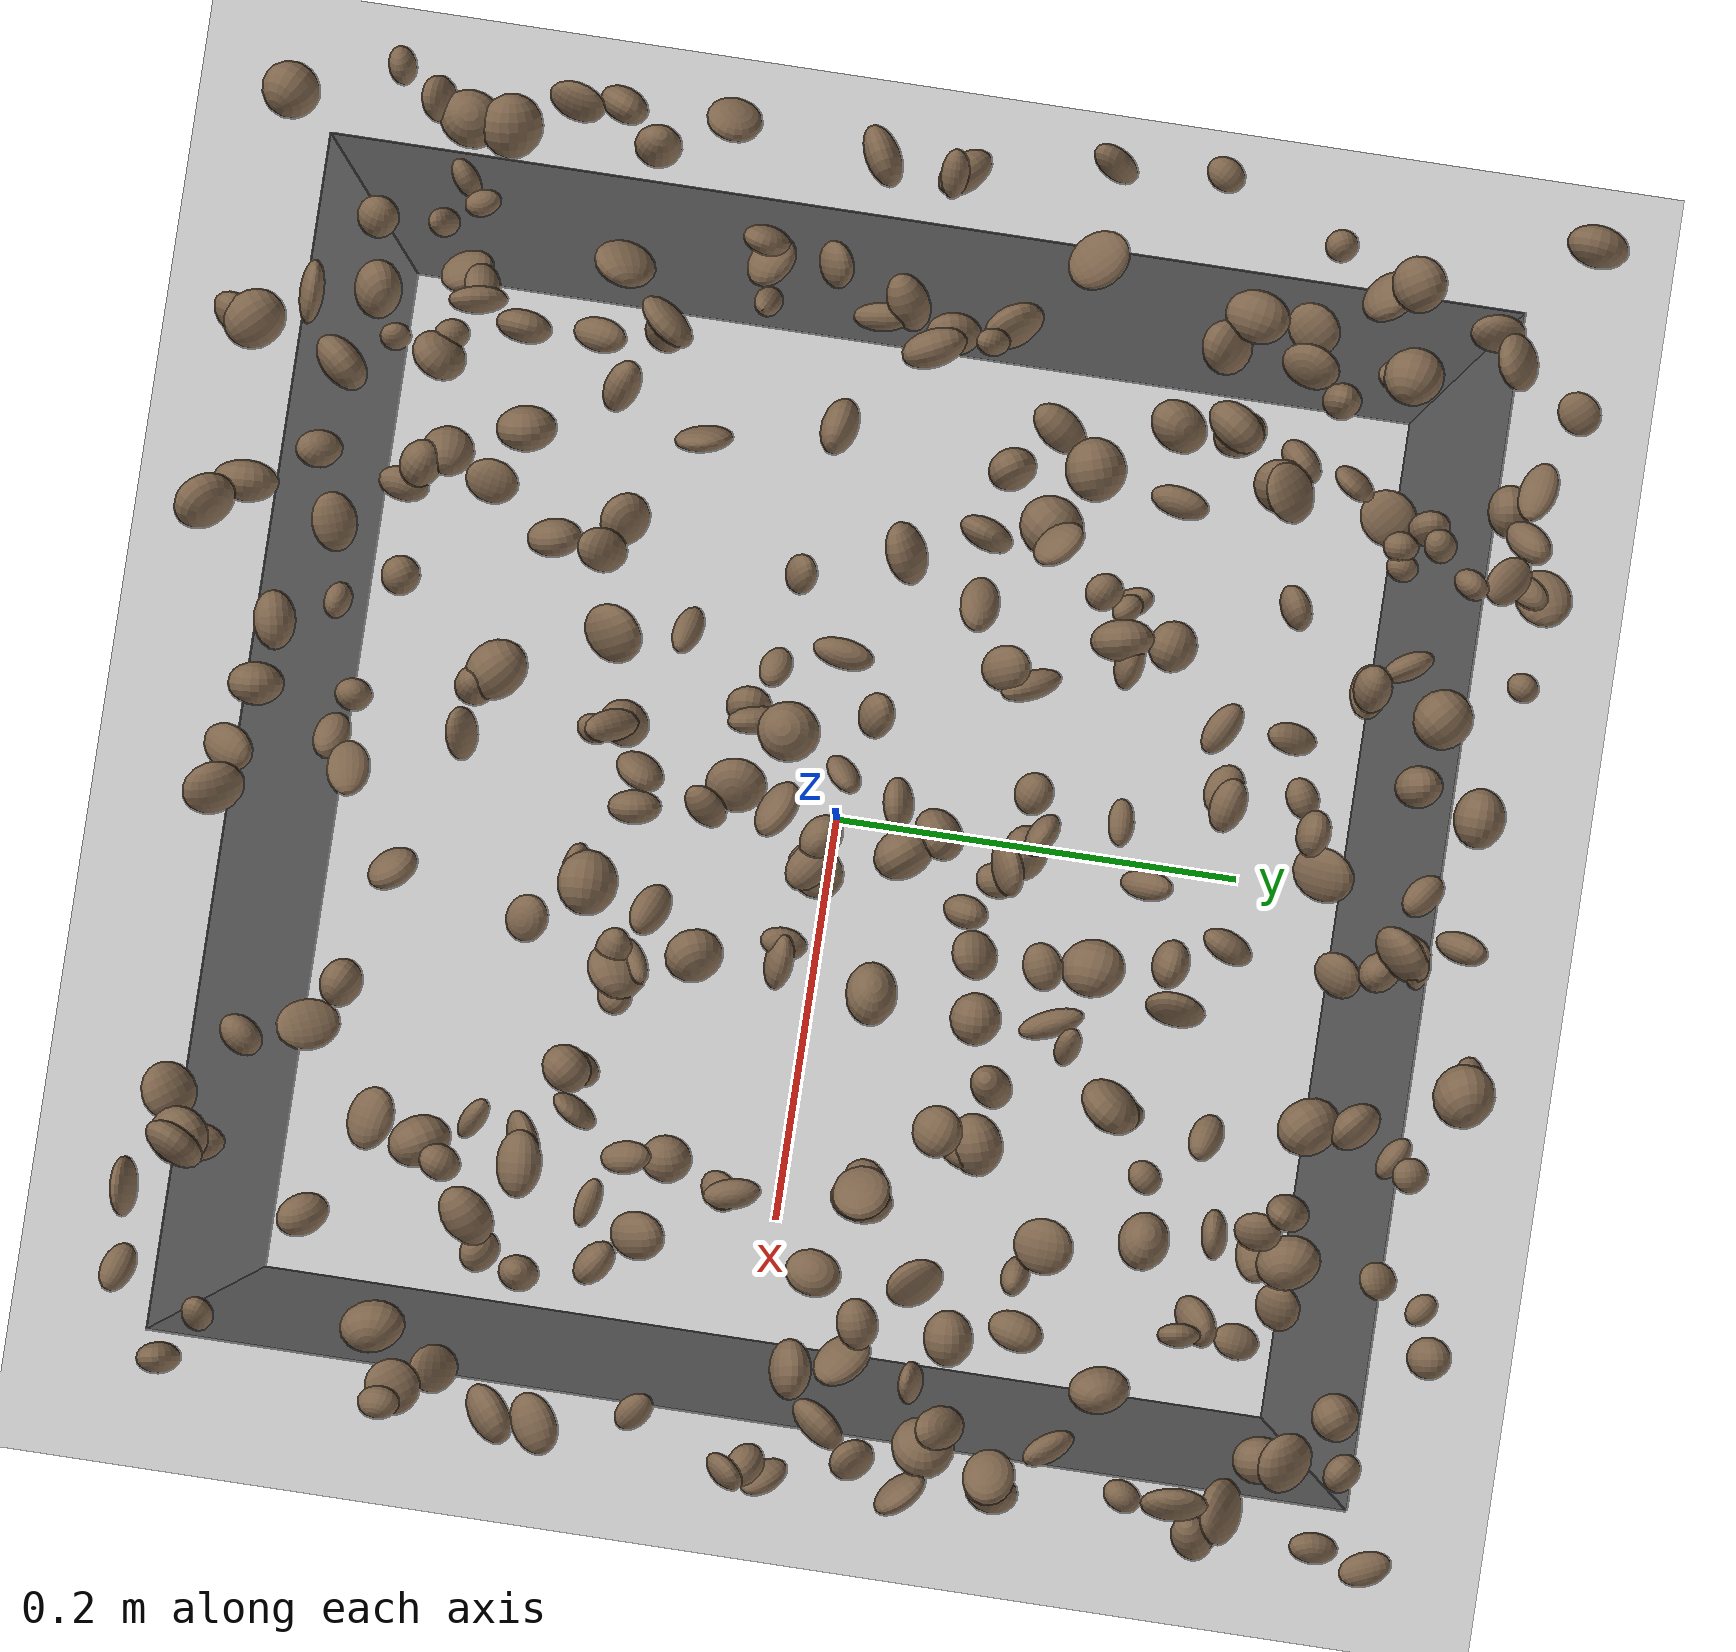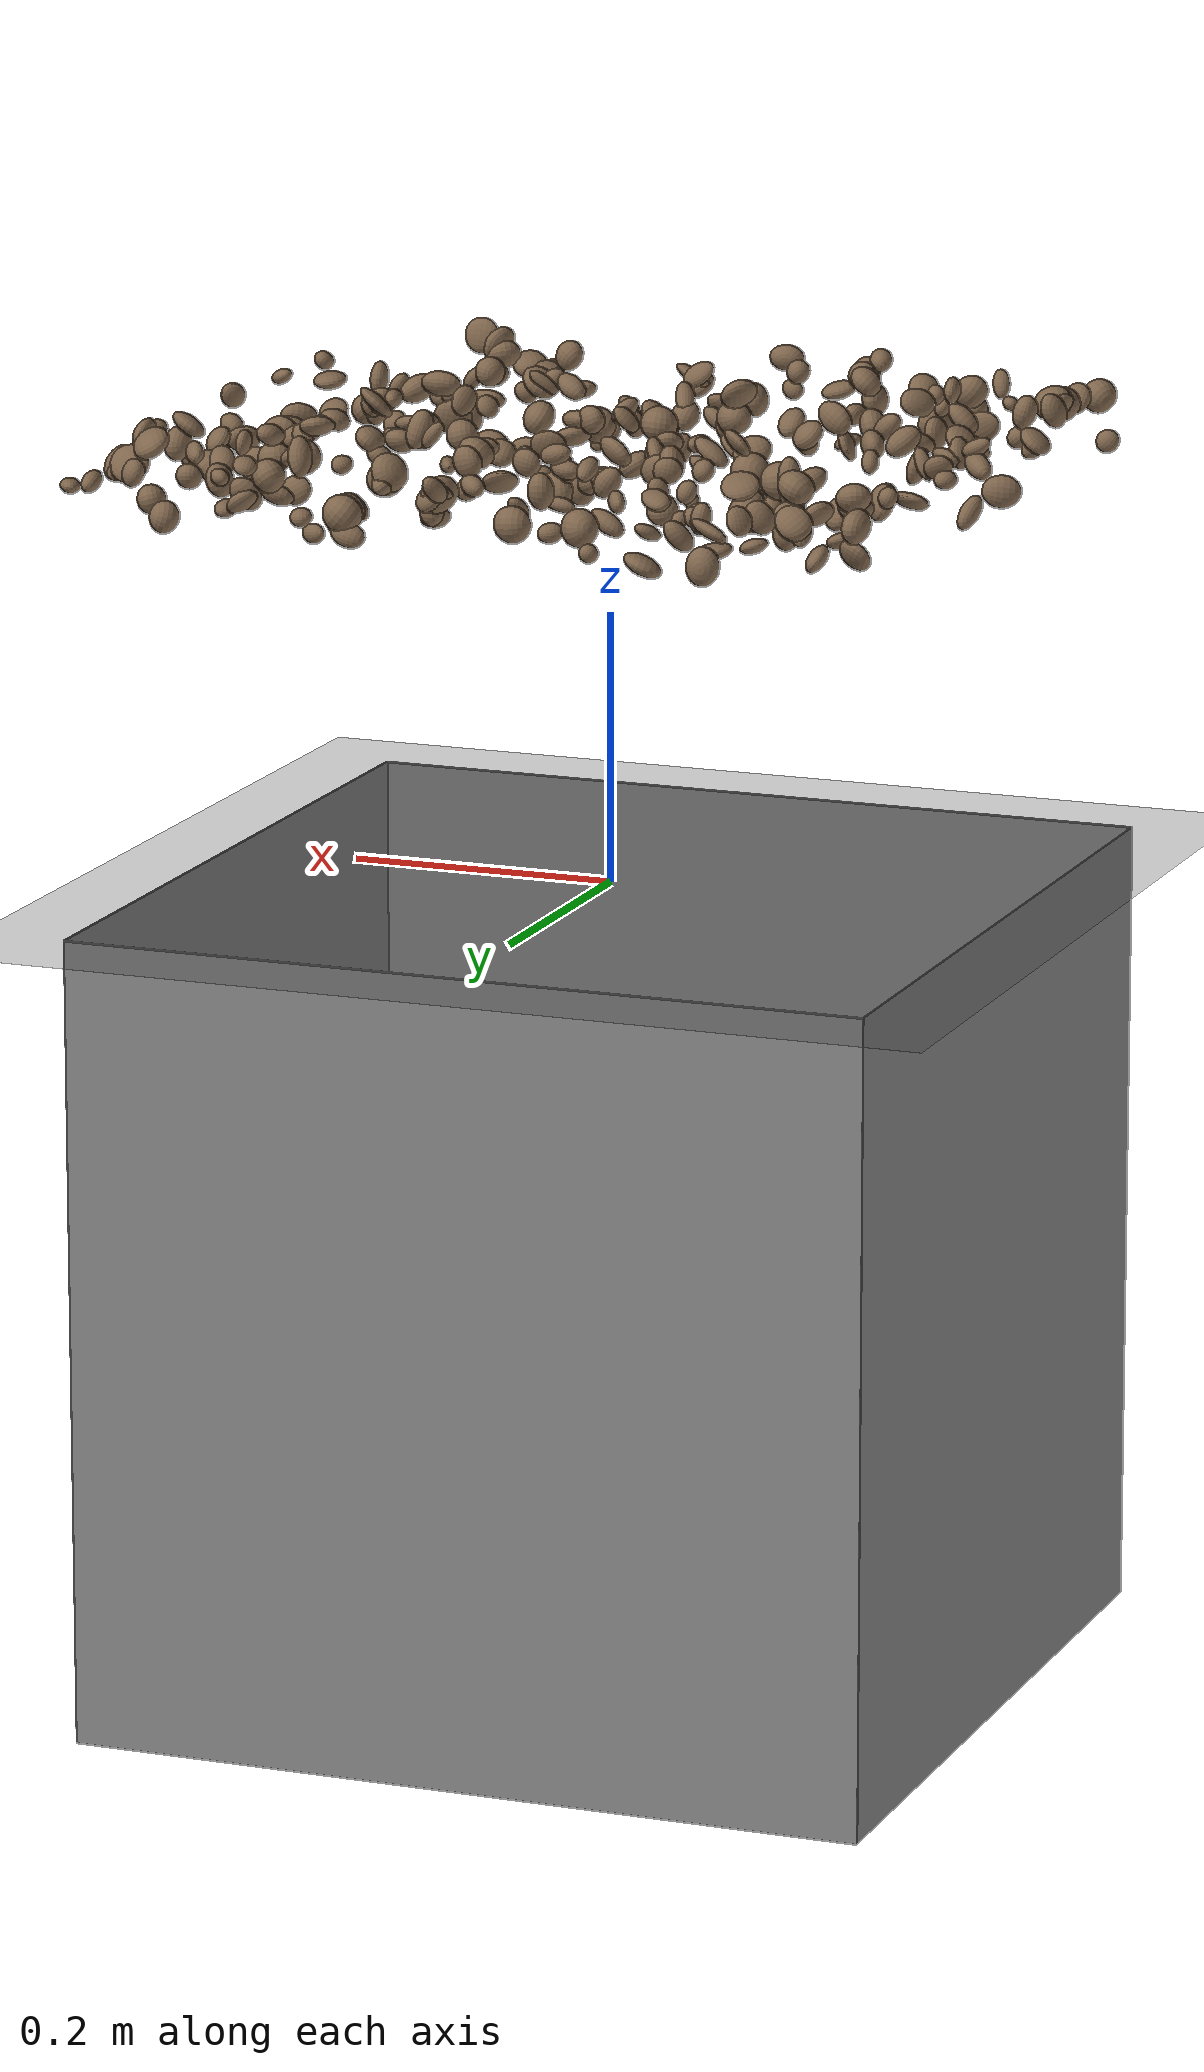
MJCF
<mujoco model="rocky_terrain_scene">
    <compiler angle="radian" inertiafromgeom="true" />
    <option timestep="0.002" gravity="0 0 -9.81" />

    <worldbody>
        <light name="sunlight" pos="5 5 5" dir="-1 -1 -1" diffuse="1 1 1" specular="0.5 0.5 0.5"
            ambient="0.5 0.5 0.5" />

        <geom name="ground_plane" type="plane" size="50 50 0.1" rgba="0.3 0.3 0.3 1" />

        <body name="rocky_terrain_body">

        </body>
        <body name="rock1" pos="-0.10992358852590958 -0.11093423427800492 0.31762898592550803">
            <joint type="free" />
            <geom type="ellipsoid"
                size="0.01176080419600127 0.012543583028663399 0.008105148927573134"
                quat="0.3033596453657238 0.023348361442549512 0.22342932151675995 0.44986267167496674"
                rgba="0.5 0.4 0.3 1" />
            <inertial pos="-0.10992358852590958 -0.11093423427800492 0.31762898592550803"
                quat="0.3033596453657238 0.023348361442549512 0.22342932151675995 0.44986267167496674"
                mass="6.163116969630884e-05" />
        </body>
        <body name="rock2" pos="-0.08872201604912033 0.11344575297091086 0.3360084125254595">
            <joint type="free" />
            <geom type="ellipsoid"
                size="0.012829238329897408 0.014744528395168686 0.009224438733263996"
                quat="0.3340460970623387 0.10505610803628292 0.3855143033112719 0.17538349159010647"
                rgba="0.5 0.4 0.3 1" />
            <inertial pos="-0.08872201604912033 0.11344575297091086 0.3360084125254595"
                quat="0.3340460970623387 0.10505610803628292 0.3855143033112719 0.17538349159010647"
                mass="3.5143103272648664e-05" />
        </body>
        <body name="rock3" pos="0.2820138487728951 0.1101162281240321 0.33794622893547566">
            <joint type="free" />
            <geom type="ellipsoid"
                size="0.011660496976716762 0.013497584979377947 0.006481108301383268"
                quat="0.07544505665826211 0.34581663104659227 0.4209828182354208 0.15775549405972478"
                rgba="0.5 0.4 0.3 1" />
            <inertial pos="0.2820138487728951 0.1101162281240321 0.33794622893547566"
                quat="0.07544505665826211 0.34581663104659227 0.4209828182354208 0.15775549405972478"
                mass="9.055043982525226e-05" />
        </body>
        <body name="rock4" pos="-0.00034180652013277024 -0.08719274627615961 0.3290871051547321">
            <joint type="free" />
            <geom type="ellipsoid"
                size="0.01001953709633476 0.012985706923583612 0.006880887137174859"
                quat="0.2730986539991683 0.2427172201666164 0.39224263842984947 0.09194148740436577"
                rgba="0.5 0.4 0.3 1" />
            <inertial pos="-0.00034180652013277024 -0.08719274627615961 0.3290871051547321"
                quat="0.2730986539991683 0.2427172201666164 0.39224263842984947 0.09194148740436577"
                mass="1.0675862124042432e-05" />
        </body>
        <body name="rock5" pos="0.18808036859219968 -0.2631181223377578 0.3305276790511711">
            <joint type="free" />
            <geom type="ellipsoid"
                size="0.014118932249541319 0.010353757353487932 0.013375277195537438"
                quat="0.07160048936858318 0.2843905429441402 0.2846095501911893 0.35939941749608734"
                rgba="0.5 0.4 0.3 1" />
            <inertial pos="0.18808036859219968 -0.2631181223377578 0.3305276790511711"
                quat="0.07160048936858318 0.2843905429441402 0.2846095501911893 0.35939941749608734"
                mass="4.3823833436023e-05" />
        </body>
        <body name="rock6" pos="0.07299032628844054 -0.014557038652123433 0.3102830989057505">
            <joint type="free" />
            <geom type="ellipsoid"
                size="0.005983010813097397 0.010425235363742076 0.013668109341159675"
                quat="0.21616568322171334 0.2961881021803136 0.3541232047001356 0.13352300989783739"
                rgba="0.5 0.4 0.3 1" />
            <inertial pos="0.07299032628844054 -0.014557038652123433 0.3102830989057505"
                quat="0.21616568322171334 0.2961881021803136 0.3541232047001356 0.13352300989783739"
                mass="1.4263833991123623e-05" />
        </body>
        <body name="rock7" pos="0.22614958836276727 -0.1075509694950571 0.3139950347176305">
            <joint type="free" />
            <geom type="ellipsoid"
                size="0.00907978493713743 0.007912871010180771 0.012231245903238493"
                quat="0.01044815109068887 0.4988283851297643 0.43955553674678294 0.051167927032763995"
                rgba="0.5 0.4 0.3 1" />
            <inertial pos="0.22614958836276727 -0.1075509694950571 0.3139950347176305"
                quat="0.01044815109068887 0.4988283851297643 0.43955553674678294 0.051167927032763995"
                mass="9.532234985128453e-05" />
        </body>
        <body name="rock8" pos="0.0822488243229283 0.10826469906894037 0.3223591415479944">
            <joint type="free" />
            <geom type="ellipsoid"
                size="0.014886965052147424 0.005919610144663503 0.006281864026393766"
                quat="0.3312200630988056 0.08055852174761878 0.07370724384840602 0.5145141713051696"
                rgba="0.5 0.4 0.3 1" />
            <inertial pos="0.0822488243229283 0.10826469906894037 0.3223591415479944"
                quat="0.3312200630988056 0.08055852174761878 0.07370724384840602 0.5145141713051696"
                mass="8.913952095993105e-05" />
        </body>
        <body name="rock9" pos="0.08735232811462851 -0.08341071713154327 0.3476813553540359">
            <joint type="free" />
            <geom type="ellipsoid"
                size="0.013339444722192128 0.008939784972641855 0.014096924784154165"
                quat="0.3609383492039898 0.09088034236643613 0.23069199324074735 0.31748931518882667"
                rgba="0.5 0.4 0.3 1" />
            <inertial pos="0.08735232811462851 -0.08341071713154327 0.3476813553540359"
                quat="0.3609383492039898 0.09088034236643613 0.23069199324074735 0.31748931518882667"
                mass="3.7297643580693945e-05" />
        </body>
        <body name="rock10" pos="-0.0978398096124922 -0.1411912817606116 0.3067655620701001">
            <joint type="free" />
            <geom type="ellipsoid"
                size="0.01276377081031465 0.010965209188836651 0.008301711608588754"
                quat="0.11278079133789923 0.3413720127558729 0.2714241973002756 0.27442299860595226"
                rgba="0.5 0.4 0.3 1" />
            <inertial pos="-0.0978398096124922 -0.1411912817606116 0.3067655620701001"
                quat="0.11278079133789923 0.3413720127558729 0.2714241973002756 0.27442299860595226"
                mass="1.2196372301717253e-05" />
        </body>
        <body name="rock11" pos="-0.0631896305004716 0.07698741943044385 0.33678287828725906">
            <joint type="free" />
            <geom type="ellipsoid"
                size="0.014778783040556843 0.008147236796357584 0.006025428875928976"
                quat="0.22334774727067588 0.1798208569814988 0.40235196778497717 0.19447942796284812"
                rgba="0.5 0.4 0.3 1" />
            <inertial pos="-0.0631896305004716 0.07698741943044385 0.33678287828725906"
                quat="0.22334774727067588 0.1798208569814988 0.40235196778497717 0.19447942796284812"
                mass="8.278830611418022e-05" />
        </body>
        <body name="rock12" pos="0.22570869677807898 0.04350931753304599 0.32045629666937087">
            <joint type="free" />
            <geom type="ellipsoid"
                size="0.009193551506450817 0.009119136855854186 0.011602304438576601"
                quat="0.16622557571941762 0.26384326200695185 0.3058451837245313 0.26408597854909915"
                rgba="0.5 0.4 0.3 1" />
            <inertial pos="0.22570869677807898 0.04350931753304599 0.32045629666937087"
                quat="0.16622557571941762 0.26384326200695185 0.3058451837245313 0.26408597854909915"
                mass="9.541718838335385e-05" />
        </body>
        <body name="rock13" pos="0.1610527633153907 -0.13621550865146662 0.336049711834101">
            <joint type="free" />
            <geom type="ellipsoid"
                size="0.005165790401523962 0.012433592563246507 0.006169997818397156"
                quat="0.4487285013186715 0.16109047495325182 0.11444850071495935 0.27573252301311746"
                rgba="0.5 0.4 0.3 1" />
            <inertial pos="0.1610527633153907 -0.13621550865146662 0.336049711834101"
                quat="0.4487285013186715 0.16109047495325182 0.11444850071495935 0.27573252301311746"
                mass="4.053937952786862e-05" />
        </body>
        <body name="rock14" pos="-0.15528154303803424 0.13107373908980402 0.30154032105338224">
            <joint type="free" />
            <geom type="ellipsoid"
                size="0.013447532977740304 0.00735935384032581 0.0065197442517345"
                quat="0.3564762740350945 0.2009740601237471 0.12793652063216238 0.3146131452089961"
                rgba="0.5 0.4 0.3 1" />
            <inertial pos="-0.15528154303803424 0.13107373908980402 0.30154032105338224"
                quat="0.3564762740350945 0.2009740601237471 0.12793652063216238 0.3146131452089961"
                mass="9.88296567474924e-05" />
        </body>
        <body name="rock15" pos="-0.2903620812218969 0.2939546285779355 0.34070884266294604">
            <joint type="free" />
            <geom type="ellipsoid"
                size="0.01403760543708376 0.011875055748585207 0.009218522883132779"
                quat="0.30718863148176534 0.21972302698545648 0.27013448808774004 0.2029538534450382"
                rgba="0.5 0.4 0.3 1" />
            <inertial pos="-0.2903620812218969 0.2939546285779355 0.34070884266294604"
                quat="0.30718863148176534 0.21972302698545648 0.27013448808774004 0.2029538534450382"
                mass="5.5797580567033624e-05" />
        </body>
        <body name="rock16" pos="0.1634809341716234 0.19344400701511633 0.3141641907727162">
            <joint type="free" />
            <geom type="ellipsoid"
                size="0.005720472583876364 0.011436495648470872 0.010496649139081698"
                quat="0.3670608837616315 0.12133723623343362 0.09014329349570233 0.4214585865092326"
                rgba="0.5 0.4 0.3 1" />
            <inertial pos="0.1634809341716234 0.19344400701511633 0.3141641907727162"
                quat="0.3670608837616315 0.12133723623343362 0.09014329349570233 0.4214585865092326"
                mass="1.1030531240860277e-05" />
        </body>
        <body name="rock17" pos="0.086692169187366 0.29263089514060997 0.3216101662719622">
            <joint type="free" />
            <geom type="ellipsoid"
                size="0.013257508117152754 0.014557256642749913 0.013970506424124857"
                quat="0.4179792108211738 0.058065539338706895 0.23502876194236916 0.28892648789775005"
                rgba="0.5 0.4 0.3 1" />
            <inertial pos="0.086692169187366 0.29263089514060997 0.3216101662719622"
                quat="0.4179792108211738 0.058065539338706895 0.23502876194236916 0.28892648789775005"
                mass="8.594097986228557e-05" />
        </body>
        <body name="rock18" pos="-0.010459801179493744 0.1263003493662027 0.30370310342180934">
            <joint type="free" />
            <geom type="ellipsoid"
                size="0.0058356843238966906 0.005414127883297653 0.010937079128745288"
                quat="0.2308626150923399 0.24413802465697063 0.2072641851196801 0.3177351751310094"
                rgba="0.5 0.4 0.3 1" />
            <inertial pos="-0.010459801179493744 0.1263003493662027 0.30370310342180934"
                quat="0.2308626150923399 0.24413802465697063 0.2072641851196801 0.3177351751310094"
                mass="6.956043477317531e-05" />
        </body>
        <body name="rock19" pos="-0.22099386217202305 -0.001418284008672499 0.34062948600431003">
            <joint type="free" />
            <geom type="ellipsoid"
                size="0.009127546203644662 0.009358390192074763 0.014137729691200852"
                quat="0.04838093219418828 0.35618653627926383 0.34780517145033557 0.2476273600762123"
                rgba="0.5 0.4 0.3 1" />
            <inertial pos="-0.22099386217202305 -0.001418284008672499 0.34062948600431003"
                quat="0.04838093219418828 0.35618653627926383 0.34780517145033557 0.2476273600762123"
                mass="4.6046112548814025e-05" />
        </body>
        <body name="rock20" pos="0.1483159097802248 0.22172819987419606 0.3444370913677209">
            <joint type="free" />
            <geom type="ellipsoid"
                size="0.009274632619499701 0.014998233024387051 0.007577150883260276"
                quat="0.24658747653707902 0.35804287398003765 0.18907159730527992 0.20629805217760347"
                rgba="0.5 0.4 0.3 1" />
            <inertial pos="0.1483159097802248 0.22172819987419606 0.3444370913677209"
                quat="0.24658747653707902 0.35804287398003765 0.18907159730527992 0.20629805217760347"
                mass="4.4347631684325596e-05" />
        </body>
        <body name="rock21" pos="-0.2990359870572893 0.08039758672042258 0.3104566362330187">
            <joint type="free" />
            <geom type="ellipsoid"
                size="0.014138184666563941 0.007830689759735944 0.0066630999533185825"
                quat="0.4170395995044582 0.16985512782562726 0.3168453183932047 0.09625995427670986"
                rgba="0.5 0.4 0.3 1" />
            <inertial pos="-0.2990359870572893 0.08039758672042258 0.3104566362330187"
                quat="0.4170395995044582 0.16985512782562726 0.3168453183932047 0.09625995427670986"
                mass="4.740195617158471e-05" />
        </body>
        <body name="rock22" pos="-0.16215519929618663 0.22391993939304783 0.3006277382084309">
            <joint type="free" />
            <geom type="ellipsoid"
                size="0.01340077304731066 0.005674393506962442 0.01219281691793368"
                quat="0.33530135368454544 0.3471349249390629 0.18794537433003608 0.12961834704635555"
                rgba="0.5 0.4 0.3 1" />
            <inertial pos="-0.16215519929618663 0.22391993939304783 0.3006277382084309"
                quat="0.33530135368454544 0.3471349249390629 0.18794537433003608 0.12961834704635555"
                mass="8.66618619984578e-05" />
        </body>
        <body name="rock23" pos="-0.17386768147479087 -0.2872344355007953 0.30980045775053544">
            <joint type="free" />
            <geom type="ellipsoid"
                size="0.01311389493216919 0.011057866586647177 0.014241037751180904"
                quat="0.3667114735002293 0.345094684600989 0.2093284182916413 0.07886542360714036"
                rgba="0.5 0.4 0.3 1" />
            <inertial pos="-0.17386768147479087 -0.2872344355007953 0.30980045775053544"
                quat="0.3667114735002293 0.345094684600989 0.2093284182916413 0.07886542360714036"
                mass="7.593488101377075e-05" />
        </body>
        <body name="rock24" pos="-0.1582788878683116 0.24008692529851122 0.326182611586967">
            <joint type="free" />
            <geom type="ellipsoid"
                size="0.008858612071736683 0.012206898066960702 0.007280340842643037"
                quat="0.2852835015127158 0.17391196715077903 0.27052361831922367 0.2702809130172815"
                rgba="0.5 0.4 0.3 1" />
            <inertial pos="-0.1582788878683116 0.24008692529851122 0.326182611586967"
                quat="0.2852835015127158 0.17391196715077903 0.27052361831922367 0.2702809130172815"
                mass="1.0414661582232303e-05" />
        </body>
        <body name="rock25" pos="-0.19037962642265743 -0.26503357717390036 0.301142920400739">
            <joint type="free" />
            <geom type="ellipsoid"
                size="0.005229933481329519 0.012052312243443788 0.01461193315763586"
                quat="0.2133867560127624 0.2900971529650033 0.3394403126073292 0.15707577841490508"
                rgba="0.5 0.4 0.3 1" />
            <inertial pos="-0.19037962642265743 -0.26503357717390036 0.301142920400739"
                quat="0.2133867560127624 0.2900971529650033 0.3394403126073292 0.15707577841490508"
                mass="7.026456921519947e-05" />
        </body>
        <body name="rock26" pos="0.033888698287106 0.26328285044400385 0.3304645232437864">
            <joint type="free" />
            <geom type="ellipsoid"
                size="0.005331440269330837 0.0084355329208282 0.010577244808529777"
                quat="0.08842168362162871 0.3968998186516728 0.30952903521123837 0.20514946251546015"
                rgba="0.5 0.4 0.3 1" />
            <inertial pos="0.033888698287106 0.26328285044400385 0.3304645232437864"
                quat="0.08842168362162871 0.3968998186516728 0.30952903521123837 0.20514946251546015"
                mass="8.990239840456873e-05" />
        </body>
        <body name="rock27" pos="-0.20545782895052042 0.19222751640919905 0.34963745716084194">
            <joint type="free" />
            <geom type="ellipsoid"
                size="0.008462065190968081 0.014592843957120256 0.007959505033308539"
                quat="0.27150941126300937 0.2570304441720847 0.24057215992971903 0.23088798463518687"
                rgba="0.5 0.4 0.3 1" />
            <inertial pos="-0.20545782895052042 0.19222751640919905 0.34963745716084194"
                quat="0.27150941126300937 0.2570304441720847 0.24057215992971903 0.23088798463518687"
                mass="2.780917522471998e-05" />
        </body>
        <body name="rock28" pos="0.16726457990670457 0.03650508887177306 0.3490483868641175">
            <joint type="free" />
            <geom type="ellipsoid"
                size="0.012921211389449985 0.014657249596008295 0.005333215976108565"
                quat="0.11021256935889064 0.25957133968621754 0.4568718191213223 0.17334427183356954"
                rgba="0.5 0.4 0.3 1" />
            <inertial pos="0.16726457990670457 0.03650508887177306 0.3490483868641175"
                quat="0.11021256935889064 0.25957133968621754 0.4568718191213223 0.17334427183356954"
                mass="1.1078311375950682e-05" />
        </body>
        <body name="rock29" pos="-0.2971030086884873 0.12793030042272585 0.34238257908232306">
            <joint type="free" />
            <geom type="ellipsoid"
                size="0.009002831531374673 0.006757188180592058 0.007359781040617278"
                quat="0.338735534031811 0.28930827922071456 0.1810530837257016 0.19090310302177282"
                rgba="0.5 0.4 0.3 1" />
            <inertial pos="-0.2971030086884873 0.12793030042272585 0.34238257908232306"
                quat="0.338735534031811 0.28930827922071456 0.1810530837257016 0.19090310302177282"
                mass="8.113804616149448e-05" />
        </body>
        <body name="rock30" pos="0.2926498424054858 0.25624302042732044 0.323021635315949">
            <joint type="free" />
            <geom type="ellipsoid"
                size="0.01128921731081899 0.007380908199247746 0.00661789263356361"
                quat="0.36072969187144655 0.1155128731617229 0.21719607640144512 0.3065613585653854"
                rgba="0.5 0.4 0.3 1" />
            <inertial pos="0.2926498424054858 0.25624302042732044 0.323021635315949"
                quat="0.36072969187144655 0.1155128731617229 0.21719607640144512 0.3065613585653854"
                mass="3.6578175684449086e-05" />
        </body>
        <body name="rock31" pos="-0.2214794247661046 0.04617138640584284 0.30540566516361417">
            <joint type="free" />
            <geom type="ellipsoid"
                size="0.014656909263137913 0.013653927621814919 0.007805380103380114"
                quat="0.27590561081415393 0.07584844579018701 0.3014446968370166 0.3468012465586425"
                rgba="0.5 0.4 0.3 1" />
            <inertial pos="-0.2214794247661046 0.04617138640584284 0.30540566516361417"
                quat="0.27590561081415393 0.07584844579018701 0.3014446968370166 0.3468012465586425"
                mass="6.586724112875125e-05" />
        </body>
        <body name="rock32" pos="0.17733789400719785 -0.025137576273505713 0.3098469903687578">
            <joint type="free" />
            <geom type="ellipsoid"
                size="0.012042935331893528 0.0058008447144174465 0.00825314729687596"
                quat="0.146270327257412 0.4311276487832614 0.12372952519548598 0.29887249876384064"
                rgba="0.5 0.4 0.3 1" />
            <inertial pos="0.17733789400719785 -0.025137576273505713 0.3098469903687578"
                quat="0.146270327257412 0.4311276487832614 0.12372952519548598 0.29887249876384064"
                mass="6.015623003816165e-05" />
        </body>
        <body name="rock33" pos="0.11340256682710381 0.08571436981638664 0.34174691216991326">
            <joint type="free" />
            <geom type="ellipsoid"
                size="0.008603091954352753 0.009169698401333477 0.014857988028227003"
                quat="0.057245032352638885 0.20304430452210848 0.6300003694980044 0.1097102936272482"
                rgba="0.5 0.4 0.3 1" />
            <inertial pos="0.11340256682710381 0.08571436981638664 0.34174691216991326"
                quat="0.057245032352638885 0.20304430452210848 0.6300003694980044 0.1097102936272482"
                mass="7.655429249914361e-05" />
        </body>
        <body name="rock34" pos="0.25766379391480226 0.262885728319798 0.33285218151006385">
            <joint type="free" />
            <geom type="ellipsoid"
                size="0.007376344491419639 0.010617613320174628 0.009040406573491791"
                quat="0.36418058901958905 0.30528371632992546 0.09805531141511872 0.2324803832353668"
                rgba="0.5 0.4 0.3 1" />
            <inertial pos="0.25766379391480226 0.262885728319798 0.33285218151006385"
                quat="0.36418058901958905 0.30528371632992546 0.09805531141511872 0.2324803832353668"
                mass="4.544931031472142e-05" />
        </body>
        <body name="rock35" pos="-0.27909760484516644 -0.21831139100983685 0.33712282141486344">
            <joint type="free" />
            <geom type="ellipsoid"
                size="0.011836590979925992 0.006399609988798681 0.010161213602243153"
                quat="0.4405992822066095 0.09502980295350406 0.36818194556741574 0.09618896927247081"
                rgba="0.5 0.4 0.3 1" />
            <inertial pos="-0.27909760484516644 -0.21831139100983685 0.33712282141486344"
                quat="0.4405992822066095 0.09502980295350406 0.36818194556741574 0.09618896927247081"
                mass="4.9060843522077086e-05" />
        </body>
        <body name="rock36" pos="0.03812868966862254 0.2480850367727349 0.31886029596966364">
            <joint type="free" />
            <geom type="ellipsoid"
                size="0.009858177006257149 0.008498469372753493 0.010856046710525764"
                quat="0.005879882860681058 0.3108578301474617 0.6786510855509278 0.004611201440929474"
                rgba="0.5 0.4 0.3 1" />
            <inertial pos="0.03812868966862254 0.2480850367727349 0.31886029596966364"
                quat="0.005879882860681058 0.3108578301474617 0.6786510855509278 0.004611201440929474"
                mass="4.8193111011235426e-05" />
        </body>
        <body name="rock37" pos="-0.21444238186737924 0.02045237159871993 0.30241878024323215">
            <joint type="free" />
            <geom type="ellipsoid"
                size="0.013184721442272382 0.010699108114992258 0.008871546794139097"
                quat="0.37001798525948504 0.08511884397485323 0.2811492280265135 0.2637139427391482"
                rgba="0.5 0.4 0.3 1" />
            <inertial pos="-0.21444238186737924 0.02045237159871993 0.30241878024323215"
                quat="0.37001798525948504 0.08511884397485323 0.2811492280265135 0.2637139427391482"
                mass="5.897559335150444e-05" />
        </body>
        <body name="rock38" pos="-0.004083787009141082 0.027296302421541907 0.302396956785705">
            <joint type="free" />
            <geom type="ellipsoid"
                size="0.006701914628874951 0.00991588441629913 0.011832607482026764"
                quat="0.2279125124308949 0.22990815258901887 0.2176442337576585 0.3245351012224277"
                rgba="0.5 0.4 0.3 1" />
            <inertial pos="-0.004083787009141082 0.027296302421541907 0.302396956785705"
                quat="0.2279125124308949 0.22990815258901887 0.2176442337576585 0.3245351012224277"
                mass="9.502016718109951e-05" />
        </body>
        <body name="rock39" pos="0.01753639391006534 -0.21367971418558357 0.33507471099497405">
            <joint type="free" />
            <geom type="ellipsoid"
                size="0.009675440226895829 0.005025666624437159 0.014046969379325154"
                quat="0.2742926826486586 0.16723513786406188 0.19203013005758454 0.3664420494296949"
                rgba="0.5 0.4 0.3 1" />
            <inertial pos="0.01753639391006534 -0.21367971418558357 0.33507471099497405"
                quat="0.2742926826486586 0.16723513786406188 0.19203013005758454 0.3664420494296949"
                mass="2.92701602772324e-05" />
        </body>
        <body name="rock40" pos="0.05910693612114948 -0.07285223332095328 0.3484156999899967">
            <joint type="free" />
            <geom type="ellipsoid"
                size="0.007305474066609885 0.008341424431280905 0.01295435020514851"
                quat="0.2412835214893921 0.2912966581361811 0.022616751235453498 0.44480306913897333"
                rgba="0.5 0.4 0.3 1" />
            <inertial pos="0.05910693612114948 -0.07285223332095328 0.3484156999899967"
                quat="0.2412835214893921 0.2912966581361811 0.022616751235453498 0.44480306913897333"
                mass="9.804939007074529e-05" />
        </body>
        <body name="rock41" pos="0.215243376070472 -0.20611162549540116 0.3084420541951761">
            <joint type="free" />
            <geom type="ellipsoid"
                size="0.012165825195607459 0.009095993558406505 0.00909051379534338"
                quat="0.1722118619139438 0.20144803717581397 0.4401624872893922 0.18617761362084995"
                rgba="0.5 0.4 0.3 1" />
            <inertial pos="0.215243376070472 -0.20611162549540116 0.3084420541951761"
                quat="0.1722118619139438 0.20144803717581397 0.4401624872893922 0.18617761362084995"
                mass="7.202441299651524e-05" />
        </body>
        <body name="rock42" pos="-0.10432936548965702 0.11464361490962516 0.3114401749489683">
            <joint type="free" />
            <geom type="ellipsoid"
                size="0.006696955527301823 0.008087486542548579 0.005655669106902652"
                quat="0.008102852749067371 0.3514700403816607 0.30092794720989735 0.33949915965937455"
                rgba="0.5 0.4 0.3 1" />
            <inertial pos="-0.10432936548965702 0.11464361490962516 0.3114401749489683"
                quat="0.008102852749067371 0.3514700403816607 0.30092794720989735 0.33949915965937455"
                mass="9.020248067891063e-05" />
        </body>
        <body name="rock43" pos="-0.05508713104592955 -0.23016039532065544 0.3264119731699573">
            <joint type="free" />
            <geom type="ellipsoid"
                size="0.00600506670117572 0.008412735522384989 0.0073729527301244786"
                quat="0.07484237820657363 0.44195793089261665 0.3790824874123102 0.10411720348849945"
                rgba="0.5 0.4 0.3 1" />
            <inertial pos="-0.05508713104592955 -0.23016039532065544 0.3264119731699573"
                quat="0.07484237820657363 0.44195793089261665 0.3790824874123102 0.10411720348849945"
                mass="8.49501335551493e-05" />
        </body>
        <body name="rock44" pos="-0.09613949592257645 0.23973155318120504 0.33333848240242836">
            <joint type="free" />
            <geom type="ellipsoid"
                size="0.011836405739262423 0.007990662483007744 0.005711715471167585"
                quat="0.19347379372480608 0.17016147315352298 0.3296351005511939 0.3067296325704771"
                rgba="0.5 0.4 0.3 1" />
            <inertial pos="-0.09613949592257645 0.23973155318120504 0.33333848240242836"
                quat="0.19347379372480608 0.17016147315352298 0.3296351005511939 0.3067296325704771"
                mass="1.2627340316009488e-05" />
        </body>
        <body name="rock45" pos="0.21754275232663295 0.1123271849536312 0.335569673255255">
            <joint type="free" />
            <geom type="ellipsoid"
                size="0.012568028441764943 0.007792598450492896 0.008656947044807434"
                quat="0.2832058519148907 0.28419342758760346 0.16075469606618503 0.27184602443132067"
                rgba="0.5 0.4 0.3 1" />
            <inertial pos="0.21754275232663295 0.1123271849536312 0.335569673255255"
                quat="0.2832058519148907 0.28419342758760346 0.16075469606618503 0.27184602443132067"
                mass="3.071625351679566e-05" />
        </body>
        <body name="rock46" pos="0.17037335247376179 0.16211749229413508 0.33189302084620814">
            <joint type="free" />
            <geom type="ellipsoid"
                size="0.011183198478927821 0.012882443682445711 0.012544325146542922"
                quat="0.08972498991941355 0.4412398080100481 0.4012121256701859 0.0678230764003524"
                rgba="0.5 0.4 0.3 1" />
            <inertial pos="0.17037335247376179 0.16211749229413508 0.33189302084620814"
                quat="0.08972498991941355 0.4412398080100481 0.4012121256701859 0.0678230764003524"
                mass="7.621023152509915e-05" />
        </body>
        <body name="rock47" pos="0.017047563609105643 -0.004089743979557636 0.33930683068524514">
            <joint type="free" />
            <geom type="ellipsoid"
                size="0.008569353603475235 0.011327025171234545 0.010401075180478538"
                quat="0.5165445259044412 0.07454149994713569 0.1083151096412899 0.30059886450713313"
                rgba="0.5 0.4 0.3 1" />
            <inertial pos="0.017047563609105643 -0.004089743979557636 0.33930683068524514"
                quat="0.5165445259044412 0.07454149994713569 0.1083151096412899 0.30059886450713313"
                mass="6.868429230022472e-05" />
        </body>
        <body name="rock48" pos="0.06487794771283373 -0.013573797188372427 0.31049185465252355">
            <joint type="free" />
            <geom type="ellipsoid"
                size="0.010702331465751818 0.007054694594192317 0.006563053984004293"
                quat="0.44632700873900955 0.040620773952161335 0.12710062359325391 0.38595159371557514"
                rgba="0.5 0.4 0.3 1" />
            <inertial pos="0.06487794771283373 -0.013573797188372427 0.31049185465252355"
                quat="0.44632700873900955 0.040620773952161335 0.12710062359325391 0.38595159371557514"
                mass="9.233697975029056e-05" />
        </body>
        <body name="rock49" pos="0.21299122241013074 -0.2825090967344146 0.34020538828299485">
            <joint type="free" />
            <geom type="ellipsoid"
                size="0.005162878883775204 0.013738155492038936 0.013233509210009715"
                quat="0.22447730234083005 0.2503097676856869 0.23580428835053632 0.2894086416229467"
                rgba="0.5 0.4 0.3 1" />
            <inertial pos="0.21299122241013074 -0.2825090967344146 0.34020538828299485"
                quat="0.22447730234083005 0.2503097676856869 0.23580428835053632 0.2894086416229467"
                mass="5.333936827663673e-05" />
        </body>
        <body name="rock50" pos="0.20286033937040143 0.19142590620313332 0.3083295114353062">
            <joint type="free" />
            <geom type="ellipsoid"
                size="0.0072637113910898705 0.010702599969594214 0.014193428049844352"
                quat="0.3424721594422035 0.005272726996078105 0.1941787855310546 0.45807632803066384"
                rgba="0.5 0.4 0.3 1" />
            <inertial pos="0.20286033937040143 0.19142590620313332 0.3083295114353062"
                quat="0.3424721594422035 0.005272726996078105 0.1941787855310546 0.45807632803066384"
                mass="1.9242012113829386e-05" />
        </body>
        <body name="rock51" pos="-0.08009800521402458 0.11820159141232323 0.33228877050789324">
            <joint type="free" />
            <geom type="ellipsoid"
                size="0.0062962230011669 0.013250050701293148 0.010732527824544414"
                quat="0.3926873487223151 0.08918767847478083 0.15051126474171317 0.367613708061191"
                rgba="0.5 0.4 0.3 1" />
            <inertial pos="-0.08009800521402458 0.11820159141232323 0.33228877050789324"
                quat="0.3926873487223151 0.08918767847478083 0.15051126474171317 0.367613708061191"
                mass="9.711262474897036e-05" />
        </body>
        <body name="rock52" pos="-0.13964752218944712 0.23126958792261326 0.3220484390145957">
            <joint type="free" />
            <geom type="ellipsoid"
                size="0.007193983334744871 0.0067682315335291674 0.005999663729201816"
                quat="0.3701053378303445 0.185809809192707 0.2355920080784977 0.2084928448984509"
                rgba="0.5 0.4 0.3 1" />
            <inertial pos="-0.13964752218944712 0.23126958792261326 0.3220484390145957"
                quat="0.3701053378303445 0.185809809192707 0.2355920080784977 0.2084928448984509"
                mass="2.1368741900778275e-05" />
        </body>
        <body name="rock53" pos="0.16857352313482477 -0.1825334136819609 0.3121358367885257">
            <joint type="free" />
            <geom type="ellipsoid"
                size="0.014315413798219254 0.006812174703079061 0.011139042088156317"
                quat="0.043474823863965985 0.05488551776083065 0.3344123473087618 0.5672273110664416"
                rgba="0.5 0.4 0.3 1" />
            <inertial pos="0.16857352313482477 -0.1825334136819609 0.3121358367885257"
                quat="0.043474823863965985 0.05488551776083065 0.3344123473087618 0.5672273110664416"
                mass="8.977465497149461e-05" />
        </body>
        <body name="rock54" pos="0.2358919411792048 0.25929144189614256 0.3022740704876102">
            <joint type="free" />
            <geom type="ellipsoid"
                size="0.010453212029525021 0.011898000118589203 0.01075018226253978"
                quat="0.1850318289695899 0.1550642604667529 0.27870928564961955 0.38119462491403766"
                rgba="0.5 0.4 0.3 1" />
            <inertial pos="0.2358919411792048 0.25929144189614256 0.3022740704876102"
                quat="0.1850318289695899 0.1550642604667529 0.27870928564961955 0.38119462491403766"
                mass="6.7923519773298e-05" />
        </body>
        <body name="rock55" pos="0.026028748555841585 0.2576067214476086 0.336355280000737">
            <joint type="free" />
            <geom type="ellipsoid"
                size="0.010946985261174623 0.0050715832639539075 0.006880977756122793"
                quat="0.3815501585782326 0.24947020453903543 0.04269697496148797 0.32628266192124394"
                rgba="0.5 0.4 0.3 1" />
            <inertial pos="0.026028748555841585 0.2576067214476086 0.336355280000737"
                quat="0.3815501585782326 0.24947020453903543 0.04269697496148797 0.32628266192124394"
                mass="8.194689715272677e-05" />
        </body>
        <body name="rock56" pos="0.17867795641020529 0.11844674423667767 0.34560147723859164">
            <joint type="free" />
            <geom type="ellipsoid"
                size="0.006886495320338764 0.01354992339327598 0.012441488102997809"
                quat="0.39079419394985715 0.07283747421540468 0.47628740953612614 0.060080922298612026"
                rgba="0.5 0.4 0.3 1" />
            <inertial pos="0.17867795641020529 0.11844674423667767 0.34560147723859164"
                quat="0.39079419394985715 0.07283747421540468 0.47628740953612614 0.060080922298612026"
                mass="6.205263303311568e-05" />
        </body>
        <body name="rock57" pos="0.017717224200845982 0.07857445049395256 0.33546785026410847">
            <joint type="free" />
            <geom type="ellipsoid"
                size="0.00519636327800267 0.01238592946075586 0.012875751527453051"
                quat="0.29718865667043765 0.10691704515219044 0.28748726017128157 0.30840703800609026"
                rgba="0.5 0.4 0.3 1" />
            <inertial pos="0.017717224200845982 0.07857445049395256 0.33546785026410847"
                quat="0.29718865667043765 0.10691704515219044 0.28748726017128157 0.30840703800609026"
                mass="5.985175644562531e-05" />
        </body>
        <body name="rock58" pos="0.17024961274520434 0.2262316949365069 0.33014537023768975">
            <joint type="free" />
            <geom type="ellipsoid"
                size="0.011825476624924683 0.014555556366034315 0.01210827227978228"
                quat="0.583274399430764 0.08667221970263111 0.18562530241746653 0.14442807844913844"
                rgba="0.5 0.4 0.3 1" />
            <inertial pos="0.17024961274520434 0.2262316949365069 0.33014537023768975"
                quat="0.583274399430764 0.08667221970263111 0.18562530241746653 0.14442807844913844"
                mass="5.10890636664796e-05" />
        </body>
        <body name="rock59" pos="-0.12537493355554374 0.07941725120921805 0.3477636251262599">
            <joint type="free" />
            <geom type="ellipsoid"
                size="0.0050447967363924 0.011344478232468562 0.012610130092244067"
                quat="0.4624579792887265 0.22369384978807877 0.2531325076460599 0.06071566327713493"
                rgba="0.5 0.4 0.3 1" />
            <inertial pos="-0.12537493355554374 0.07941725120921805 0.3477636251262599"
                quat="0.4624579792887265 0.22369384978807877 0.2531325076460599 0.06071566327713493"
                mass="5.544449704525771e-05" />
        </body>
        <body name="rock60" pos="-0.19370503669626757 -0.18778183837731632 0.3425974915007057">
            <joint type="free" />
            <geom type="ellipsoid"
                size="0.013074677665454858 0.009412872759308799 0.0059599873129702954"
                quat="0.2514494874317677 0.20416153567513448 0.28446462707551656 0.2599243498175813"
                rgba="0.5 0.4 0.3 1" />
            <inertial pos="-0.19370503669626757 -0.18778183837731632 0.3425974915007057"
                quat="0.2514494874317677 0.20416153567513448 0.28446462707551656 0.2599243498175813"
                mass="8.633183352377796e-05" />
        </body>
        <body name="rock61" pos="0.20402926953716166 -0.13346987184638218 0.32660145492721315">
            <joint type="free" />
            <geom type="ellipsoid"
                size="0.011147225973991228 0.009644984595440435 0.014798437595095165"
                quat="0.03694399881610086 0.3075080473729338 0.3497438722167066 0.3058040815942588"
                rgba="0.5 0.4 0.3 1" />
            <inertial pos="0.20402926953716166 -0.13346987184638218 0.32660145492721315"
                quat="0.03694399881610086 0.3075080473729338 0.3497438722167066 0.3058040815942588"
                mass="8.890223570575695e-05" />
        </body>
        <body name="rock62" pos="-0.10877453962551936 0.10276254719707434 0.3308675247699297">
            <joint type="free" />
            <geom type="ellipsoid"
                size="0.008764393199399504 0.007500185417359906 0.008623856189821685"
                quat="0.294252589598116 0.2625935745555971 0.39589344804048865 0.0472603878057982"
                rgba="0.5 0.4 0.3 1" />
            <inertial pos="-0.10877453962551936 0.10276254719707434 0.3308675247699297"
                quat="0.294252589598116 0.2625935745555971 0.39589344804048865 0.0472603878057982"
                mass="6.285721996152359e-05" />
        </body>
        <body name="rock63" pos="0.28104139597438843 0.19123143705239903 0.34683677210624403">
            <joint type="free" />
            <geom type="ellipsoid"
                size="0.014776845593572879 0.006365362435133724 0.011328399370575441"
                quat="0.08428867439530767 0.38821698948425687 0.43057601815239016 0.09691831796804536"
                rgba="0.5 0.4 0.3 1" />
            <inertial pos="0.28104139597438843 0.19123143705239903 0.34683677210624403"
                quat="0.08428867439530767 0.38821698948425687 0.43057601815239016 0.09691831796804536"
                mass="4.757210374193401e-05" />
        </body>
        <body name="rock64" pos="0.05135801360401293 -0.10327045456441067 0.3156466325295479">
            <joint type="free" />
            <geom type="ellipsoid"
                size="0.013522922891286284 0.013105623381858188 0.014571187278248264"
                quat="0.3363511876352359 0.16538410120320607 0.3064078641401471 0.19185684702141093"
                rgba="0.5 0.4 0.3 1" />
            <inertial pos="0.05135801360401293 -0.10327045456441067 0.3156466325295479"
                quat="0.3363511876352359 0.16538410120320607 0.3064078641401471 0.19185684702141093"
                mass="6.13154833642321e-05" />
        </body>
        <body name="rock65" pos="0.2919342491939149 -0.09136170833293003 0.3004064762627537">
            <joint type="free" />
            <geom type="ellipsoid"
                size="0.010489813687247544 0.006992108005526478 0.014314328043324206"
                quat="0.12888142609875178 0.2356159668101517 0.27439888773137056 0.361103719359726"
                rgba="0.5 0.4 0.3 1" />
            <inertial pos="0.2919342491939149 -0.09136170833293003 0.3004064762627537"
                quat="0.12888142609875178 0.2356159668101517 0.27439888773137056 0.361103719359726"
                mass="8.604954644898223e-05" />
        </body>
        <body name="rock66" pos="-0.25498054241880735 0.07914083446562908 0.3153032548464395">
            <joint type="free" />
            <geom type="ellipsoid"
                size="0.013120704355636986 0.005321077964001101 0.014782121373160713"
                quat="0.29930448375273844 0.4364031799601017 0.07435999781407995 0.18993233847307991"
                rgba="0.5 0.4 0.3 1" />
            <inertial pos="-0.25498054241880735 0.07914083446562908 0.3153032548464395"
                quat="0.29930448375273844 0.4364031799601017 0.07435999781407995 0.18993233847307991"
                mass="8.598928126507805e-05" />
        </body>
        <body name="rock67" pos="0.2599740923037203 -0.16874687471954122 0.3006863396611872">
            <joint type="free" />
            <geom type="ellipsoid"
                size="0.014866536545183454 0.011473077800496397 0.01161038848830681"
                quat="0.2962722714672648 0.15871378883237117 0.09878803802962634 0.4462259016707377"
                rgba="0.5 0.4 0.3 1" />
            <inertial pos="0.2599740923037203 -0.16874687471954122 0.3006863396611872"
                quat="0.2962722714672648 0.15871378883237117 0.09878803802962634 0.4462259016707377"
                mass="5.875552486412286e-05" />
        </body>
        <body name="rock68" pos="-0.2501112747415059 0.25924066834306453 0.3086580435147632">
            <joint type="free" />
            <geom type="ellipsoid"
                size="0.01283057284121188 0.00628991090142654 0.010021927202742538"
                quat="0.19365551807967782 0.34411941845886707 0.39294175120884584 0.06928331225260934"
                rgba="0.5 0.4 0.3 1" />
            <inertial pos="-0.2501112747415059 0.25924066834306453 0.3086580435147632"
                quat="0.19365551807967782 0.34411941845886707 0.39294175120884584 0.06928331225260934"
                mass="5.683328965284514e-05" />
        </body>
        <body name="rock69" pos="0.20191992750880644 0.2923623970524765 0.3398740429845089">
            <joint type="free" />
            <geom type="ellipsoid"
                size="0.010321057000542297 0.008509541256989704 0.009264928091366524"
                quat="0.12811788195778454 0.3328214686401393 0.19407817168731575 0.34498247771476037"
                rgba="0.5 0.4 0.3 1" />
            <inertial pos="0.20191992750880644 0.2923623970524765 0.3398740429845089"
                quat="0.12811788195778454 0.3328214686401393 0.19407817168731575 0.34498247771476037"
                mass="7.305957453973548e-05" />
        </body>
        <body name="rock70" pos="0.13654066061017545 0.0654767340640614 0.32833178225266074">
            <joint type="free" />
            <geom type="ellipsoid"
                size="0.00830468432856424 0.01171537101362376 0.01142890421720914"
                quat="0.38709786832403315 0.18580776716725422 0.4068616506898214 0.020232713818891225"
                rgba="0.5 0.4 0.3 1" />
            <inertial pos="0.13654066061017545 0.0654767340640614 0.32833178225266074"
                quat="0.38709786832403315 0.18580776716725422 0.4068616506898214 0.020232713818891225"
                mass="1.6099197021082137e-05" />
        </body>
        <body name="rock71" pos="0.010756368081926149 -0.05622476159434542 0.33739192900801007">
            <joint type="free" />
            <geom type="ellipsoid"
                size="0.00845891456057479 0.006350566347391066 0.011799590980426709"
                quat="0.004776692975934832 0.36362591599551336 0.3666666873032507 0.2649307037253012"
                rgba="0.5 0.4 0.3 1" />
            <inertial pos="0.010756368081926149 -0.05622476159434542 0.33739192900801007"
                quat="0.004776692975934832 0.36362591599551336 0.3666666873032507 0.2649307037253012"
                mass="7.730449482537836e-05" />
        </body>
        <body name="rock72" pos="0.14030021105369483 -0.2435077993644545 0.3252515009978847">
            <joint type="free" />
            <geom type="ellipsoid"
                size="0.010587498640880173 0.007693752516720588 0.008907533104344768"
                quat="0.11374646286664977 0.5706437811314147 0.30244935075778706 0.013160405244148523"
                rgba="0.5 0.4 0.3 1" />
            <inertial pos="0.14030021105369483 -0.2435077993644545 0.3252515009978847"
                quat="0.11374646286664977 0.5706437811314147 0.30244935075778706 0.013160405244148523"
                mass="2.4593167015380346e-05" />
        </body>
        <body name="rock73" pos="-0.17413461093816443 -0.29366913727672256 0.3032456632497658">
            <joint type="free" />
            <geom type="ellipsoid"
                size="0.014595049842916031 0.013305839373914004 0.008466860621407217"
                quat="0.3642717403224975 0.27402755943280704 0.16829890262249506 0.19340179762220047"
                rgba="0.5 0.4 0.3 1" />
            <inertial pos="-0.17413461093816443 -0.29366913727672256 0.3032456632497658"
                quat="0.3642717403224975 0.27402755943280704 0.16829890262249506 0.19340179762220047"
                mass="2.0247023474536928e-05" />
        </body>
        <body name="rock74" pos="-0.17324500116620806 0.27669721557495747 0.3008350217308807">
            <joint type="free" />
            <geom type="ellipsoid"
                size="0.011834691763174381 0.014192147378781921 0.009650024099443714"
                quat="0.4634841026004435 0.46413440405102085 0.016599464735072376 0.055782028613463264"
                rgba="0.5 0.4 0.3 1" />
            <inertial pos="-0.17324500116620806 0.27669721557495747 0.3008350217308807"
                quat="0.4634841026004435 0.46413440405102085 0.016599464735072376 0.055782028613463264"
                mass="6.731258906225971e-05" />
        </body>
        <body name="rock75" pos="0.1312703975750955 -0.21445427845014386 0.33004218900008253">
            <joint type="free" />
            <geom type="ellipsoid"
                size="0.01163468019256186 0.005105138121527157 0.014411878664506612"
                quat="0.4733090453349078 0.3595929815104009 0.020933149734722167 0.1461648234199691"
                rgba="0.5 0.4 0.3 1" />
            <inertial pos="0.1312703975750955 -0.21445427845014386 0.33004218900008253"
                quat="0.4733090453349078 0.3595929815104009 0.020933149734722167 0.1461648234199691"
                mass="6.642279248011378e-05" />
        </body>
        <body name="rock76" pos="-0.030270154018778195 0.16736161171293118 0.3381730327223828">
            <joint type="free" />
            <geom type="ellipsoid"
                size="0.008557993879817559 0.007055557874823613 0.011619239912077322"
                quat="0.28193068390269416 0.28902808983453643 0.18629202828334893 0.24274919797942054"
                rgba="0.5 0.4 0.3 1" />
            <inertial pos="-0.030270154018778195 0.16736161171293118 0.3381730327223828"
                quat="0.28193068390269416 0.28902808983453643 0.18629202828334893 0.24274919797942054"
                mass="2.897483475504699e-05" />
        </body>
        <body name="rock77" pos="-0.15859660915123766 0.0551931891048793 0.30351073722577393">
            <joint type="free" />
            <geom type="ellipsoid"
                size="0.010995741007089003 0.014980835873544346 0.009288057465114581"
                quat="0.16492672539573955 0.18681127301032904 0.3046565542588178 0.3436054473351135"
                rgba="0.5 0.4 0.3 1" />
            <inertial pos="-0.15859660915123766 0.0551931891048793 0.30351073722577393"
                quat="0.16492672539573955 0.18681127301032904 0.3046565542588178 0.3436054473351135"
                mass="4.804367191250802e-05" />
        </body>
        <body name="rock78" pos="0.015321399338561692 0.14177329896116314 0.30211012984322866">
            <joint type="free" />
            <geom type="ellipsoid"
                size="0.00590297514494689 0.013799329457791082 0.00666901837922462"
                quat="0.388281833182326 0.13954977633150317 0.3617004623218508 0.11046792816431995"
                rgba="0.5 0.4 0.3 1" />
            <inertial pos="0.015321399338561692 0.14177329896116314 0.30211012984322866"
                quat="0.388281833182326 0.13954977633150317 0.3617004623218508 0.11046792816431995"
                mass="8.404606599600892e-05" />
        </body>
        <body name="rock79" pos="0.19157328262876316 -0.2639884150792502 0.33801374495410347">
            <joint type="free" />
            <geom type="ellipsoid"
                size="0.01453133466292177 0.013656022299024375 0.00739562067555477"
                quat="0.4584337989972016 0.18859143608717904 0.2777449378070394 0.07522982710857991"
                rgba="0.5 0.4 0.3 1" />
            <inertial pos="0.19157328262876316 -0.2639884150792502 0.33801374495410347"
                quat="0.4584337989972016 0.18859143608717904 0.2777449378070394 0.07522982710857991"
                mass="8.035993480107367e-05" />
        </body>
        <body name="rock80" pos="0.1686234156403411 -0.06832486385591444 0.3166504803459851">
            <joint type="free" />
            <geom type="ellipsoid"
                size="0.011834209638830428 0.0059388237199796915 0.007496812535398755"
                quat="0.23291354126110428 0.24248480545265674 0.1594105746102966 0.3651910786759424"
                rgba="0.5 0.4 0.3 1" />
            <inertial pos="0.1686234156403411 -0.06832486385591444 0.3166504803459851"
                quat="0.23291354126110428 0.24248480545265674 0.1594105746102966 0.3651910786759424"
                mass="5.124716307982022e-05" />
        </body>
        <body name="rock81" pos="0.12197488549786317 0.1843579124235062 0.30368049205983794">
            <joint type="free" />
            <geom type="ellipsoid"
                size="0.007395297777696555 0.007080551283510941 0.012445573163521378"
                quat="0.3631543761047107 0.19611559185235658 0.1211093565443093 0.31962067549862344"
                rgba="0.5 0.4 0.3 1" />
            <inertial pos="0.12197488549786317 0.1843579124235062 0.30368049205983794"
                quat="0.3631543761047107 0.19611559185235658 0.1211093565443093 0.31962067549862344"
                mass="4.0208668628662554e-05" />
        </body>
        <body name="rock82" pos="-0.004637415913041343 -0.16609838098119434 0.34536255980243435">
            <joint type="free" />
            <geom type="ellipsoid"
                size="0.008765887531930456 0.005295099890046191 0.012828156523490446"
                quat="0.24419087969767833 0.11793337122614897 0.5011140598605823 0.1367616892155904"
                rgba="0.5 0.4 0.3 1" />
            <inertial pos="-0.004637415913041343 -0.16609838098119434 0.34536255980243435"
                quat="0.24419087969767833 0.11793337122614897 0.5011140598605823 0.1367616892155904"
                mass="3.6056467337377417e-05" />
        </body>
        <body name="rock83" pos="-0.11819967379046231 -0.24618137957644173 0.34953518497256664">
            <joint type="free" />
            <geom type="ellipsoid"
                size="0.008373407994494288 0.010488382915227312 0.007770042615431313"
                quat="0.12930344197807553 0.6305040666175109 0.10327183980566058 0.13692065159875302"
                rgba="0.5 0.4 0.3 1" />
            <inertial pos="-0.11819967379046231 -0.24618137957644173 0.34953518497256664"
                quat="0.12930344197807553 0.6305040666175109 0.10327183980566058 0.13692065159875302"
                mass="2.6935006343096145e-05" />
        </body>
        <body name="rock84" pos="0.2874197447799713 -0.25966286443761666 0.306235253524268">
            <joint type="free" />
            <geom type="ellipsoid"
                size="0.009791934738249075 0.013311089591870624 0.006956162885804201"
                quat="0.21925727749082546 0.2294905373950681 0.2551578388164897 0.2960943462976167"
                rgba="0.5 0.4 0.3 1" />
            <inertial pos="0.2874197447799713 -0.25966286443761666 0.306235253524268"
                quat="0.21925727749082546 0.2294905373950681 0.2551578388164897 0.2960943462976167"
                mass="4.370571261207629e-05" />
        </body>
        <body name="rock85" pos="-0.2247255810431204 -0.2074342107616287 0.34589847173244903">
            <joint type="free" />
            <geom type="ellipsoid"
                size="0.011181746959327284 0.005424379542593678 0.006386134032973908"
                quat="0.3895749302463671 0.022437591859214203 0.44306064093001807 0.14492683696440067"
                rgba="0.5 0.4 0.3 1" />
            <inertial pos="-0.2247255810431204 -0.2074342107616287 0.34589847173244903"
                quat="0.3895749302463671 0.022437591859214203 0.44306064093001807 0.14492683696440067"
                mass="2.8252614682590838e-05" />
        </body>
        <body name="rock86" pos="0.002689317515758183 0.2600166215598095 0.34136760129747784">
            <joint type="free" />
            <geom type="ellipsoid"
                size="0.007328270019153954 0.007204245327128813 0.011024870052920542"
                quat="0.4049893399845727 0.2794044070813326 0.1940256854552809 0.12158056747881388"
                rgba="0.5 0.4 0.3 1" />
            <inertial pos="0.002689317515758183 0.2600166215598095 0.34136760129747784"
                quat="0.4049893399845727 0.2794044070813326 0.1940256854552809 0.12158056747881388"
                mass="6.98556951159725e-05" />
        </body>
        <body name="rock87" pos="0.29557035254023517 0.20241223574313488 0.32663379245316626">
            <joint type="free" />
            <geom type="ellipsoid"
                size="0.00916028920447418 0.008807358643819659 0.01418010920152981"
                quat="0.015041794097826362 0.4823391584314429 0.324071965810162 0.17854708166056862"
                rgba="0.5 0.4 0.3 1" />
            <inertial pos="0.29557035254023517 0.20241223574313488 0.32663379245316626"
                quat="0.015041794097826362 0.4823391584314429 0.324071965810162 0.17854708166056862"
                mass="6.271171744588645e-05" />
        </body>
        <body name="rock88" pos="0.28329915902686237 -0.1544072247892322 0.32379231085207166">
            <joint type="free" />
            <geom type="ellipsoid"
                size="0.012286213832882736 0.006166922058065977 0.012536642026004399"
                quat="0.1744907330008442 0.16388237492591834 0.3597222207631993 0.3019046713100382"
                rgba="0.5 0.4 0.3 1" />
            <inertial pos="0.28329915902686237 -0.1544072247892322 0.32379231085207166"
                quat="0.1744907330008442 0.16388237492591834 0.3597222207631993 0.3019046713100382"
                mass="7.361840772287583e-05" />
        </body>
        <body name="rock89" pos="-0.016052764323036817 -0.10995609039378884 0.3238846028209294">
            <joint type="free" />
            <geom type="ellipsoid"
                size="0.00794122408854588 0.0053378142349209765 0.007118183047417155"
                quat="0.19447565923294677 0.37164756942431654 0.29961738411040045 0.13425938723233624"
                rgba="0.5 0.4 0.3 1" />
            <inertial pos="-0.016052764323036817 -0.10995609039378884 0.3238846028209294"
                quat="0.19447565923294677 0.37164756942431654 0.29961738411040045 0.13425938723233624"
                mass="4.536189591652884e-05" />
        </body>
        <body name="rock90" pos="0.1937635787765103 0.10867462932957217 0.3327785203021977">
            <joint type="free" />
            <geom type="ellipsoid"
                size="0.006154051810176686 0.007673981618368119 0.011877413102611568"
                quat="0.450795933822242 0.09520778230871225 0.09213250023604257 0.36186378363300314"
                rgba="0.5 0.4 0.3 1" />
            <inertial pos="0.1937635787765103 0.10867462932957217 0.3327785203021977"
                quat="0.450795933822242 0.09520778230871225 0.09213250023604257 0.36186378363300314"
                mass="4.373496549579622e-05" />
        </body>
        <body name="rock91" pos="-0.08372048541122185 0.2254188163907928 0.31500523083417">
            <joint type="free" />
            <geom type="ellipsoid"
                size="0.013947679811125876 0.008318887386008316 0.0072162319759382695"
                quat="0.20926822892761468 0.004406964087453727 0.7359368113049383 0.05038799567999332"
                rgba="0.5 0.4 0.3 1" />
            <inertial pos="-0.08372048541122185 0.2254188163907928 0.31500523083417"
                quat="0.20926822892761468 0.004406964087453727 0.7359368113049383 0.05038799567999332"
                mass="4.7256127988938624e-05" />
        </body>
        <body name="rock92" pos="0.12489978182875439 0.275300737604067 0.31317918399968997">
            <joint type="free" />
            <geom type="ellipsoid"
                size="0.008242632576829797 0.0065416393829397365 0.007887230566199527"
                quat="0.2558004437941223 0.18056923924940174 0.33307236444197236 0.2305579525145036"
                rgba="0.5 0.4 0.3 1" />
            <inertial pos="0.12489978182875439 0.275300737604067 0.31317918399968997"
                quat="0.2558004437941223 0.18056923924940174 0.33307236444197236 0.2305579525145036"
                mass="9.123840914660652e-05" />
        </body>
        <body name="rock93" pos="0.2904089485619246 -0.11166236222939138 0.3032217393944232">
            <joint type="free" />
            <geom type="ellipsoid"
                size="0.007861526400089351 0.011695683371507198 0.014409790842359396"
                quat="0.27963562830504896 0.057033438776154105 0.3333087140497539 0.3300222188690431"
                rgba="0.5 0.4 0.3 1" />
            <inertial pos="0.2904089485619246 -0.11166236222939138 0.3032217393944232"
                quat="0.27963562830504896 0.057033438776154105 0.3333087140497539 0.3300222188690431"
                mass="2.0457405365977128e-05" />
        </body>
        <body name="rock94" pos="-0.19274521376746165 -0.23281683198175934 0.3334092167386009">
            <joint type="free" />
            <geom type="ellipsoid"
                size="0.01022910869920863 0.013427445240378741 0.012109134968542311"
                quat="0.3370472756710172 0.05459448689141149 0.23482282200412313 0.3735354154334481"
                rgba="0.5 0.4 0.3 1" />
            <inertial pos="-0.19274521376746165 -0.23281683198175934 0.3334092167386009"
                quat="0.3370472756710172 0.05459448689141149 0.23482282200412313 0.3735354154334481"
                mass="9.627925077369106e-05" />
        </body>
        <body name="rock95" pos="-0.28255361816535934 0.014650630501324868 0.33029474482235205">
            <joint type="free" />
            <geom type="ellipsoid"
                size="0.00829617087725541 0.00852363634131686 0.014235370609095965"
                quat="0.4950382446307306 0.24766386421839798 0.23969030595752783 0.01760758519334357"
                rgba="0.5 0.4 0.3 1" />
            <inertial pos="-0.28255361816535934 0.014650630501324868 0.33029474482235205"
                quat="0.4950382446307306 0.24766386421839798 0.23969030595752783 0.01760758519334357"
                mass="3.0161701029391605e-05" />
        </body>
        <body name="rock96" pos="0.05544325509768666 0.12210171278323106 0.3355289228911216">
            <joint type="free" />
            <geom type="ellipsoid"
                size="0.011141773060372746 0.014584451755469137 0.012962620330035337"
                quat="0.4749935178763309 0.11024739932249175 0.3347804185035027 0.07997866429767465"
                rgba="0.5 0.4 0.3 1" />
            <inertial pos="0.05544325509768666 0.12210171278323106 0.3355289228911216"
                quat="0.4749935178763309 0.11024739932249175 0.3347804185035027 0.07997866429767465"
                mass="3.422946356938897e-05" />
        </body>
        <body name="rock97" pos="-0.1959240767554814 -0.10426009957355356 0.34843880693556234">
            <joint type="free" />
            <geom type="ellipsoid"
                size="0.014331123508658759 0.010646765854037952 0.006276380238088127"
                quat="0.252375128183065 0.42468556014942976 0.17348634080998082 0.14945297085752446"
                rgba="0.5 0.4 0.3 1" />
            <inertial pos="-0.1959240767554814 -0.10426009957355356 0.34843880693556234"
                quat="0.252375128183065 0.42468556014942976 0.17348634080998082 0.14945297085752446"
                mass="6.438789792818518e-05" />
        </body>
        <body name="rock98" pos="-0.22095088369853433 0.2217859290827971 0.34931242551097125">
            <joint type="free" />
            <geom type="ellipsoid"
                size="0.01322739818674458 0.011445872409481663 0.013201042527462872"
                quat="0.2938641843250971 0.24545256422125913 0.13256162757664924 0.32812162387699445"
                rgba="0.5 0.4 0.3 1" />
            <inertial pos="-0.22095088369853433 0.2217859290827971 0.34931242551097125"
                quat="0.2938641843250971 0.24545256422125913 0.13256162757664924 0.32812162387699445"
                mass="7.699348008067328e-05" />
        </body>
        <body name="rock99" pos="-0.11286713305611026 0.014200235778681736 0.32825860058984">
            <joint type="free" />
            <geom type="ellipsoid"
                size="0.008152707325801384 0.011731111504253947 0.014396405917121907"
                quat="0.08171274693873622 0.3241701059638409 0.30905168121456944 0.2850654658828535"
                rgba="0.5 0.4 0.3 1" />
            <inertial pos="-0.11286713305611026 0.014200235778681736 0.32825860058984"
                quat="0.08171274693873622 0.3241701059638409 0.30905168121456944 0.2850654658828535"
                mass="3.808870113298858e-05" />
        </body>
        <body name="rock100" pos="-0.016905556667748012 0.20794523368783496 0.3494161210338989">
            <joint type="free" />
            <geom type="ellipsoid"
                size="0.007165142700479224 0.010651027699732547 0.010351983590590984"
                quat="0.31277215461554075 0.20293577970233784 0.24958131859687974 0.23471074708524167"
                rgba="0.5 0.4 0.3 1" />
            <inertial pos="-0.016905556667748012 0.20794523368783496 0.3494161210338989"
                quat="0.31277215461554075 0.20293577970233784 0.24958131859687974 0.23471074708524167"
                mass="9.742514643044025e-05" />
        </body>
        <body name="rock101" pos="-0.07640183170034051 0.2595066419117192 0.3173090594877883">
            <joint type="free" />
            <geom type="ellipsoid"
                size="0.013080669068727398 0.013792363421132617 0.013576087074995701"
                quat="0.3076207120121705 0.37737474209408145 0.14969763880571246 0.16530690708803553"
                rgba="0.5 0.4 0.3 1" />
            <inertial pos="-0.07640183170034051 0.2595066419117192 0.3173090594877883"
                quat="0.3076207120121705 0.37737474209408145 0.14969763880571246 0.16530690708803553"
                mass="5.562089830893443e-05" />
        </body>
        <body name="rock102" pos="-0.20296939239463047 0.012723922802431564 0.33940469517353195">
            <joint type="free" />
            <geom type="ellipsoid"
                size="0.008475136437214537 0.010874421889249319 0.01467772682954948"
                quat="0.39943529727675875 0.41279472480350404 0.13770004298199787 0.05006993493773936"
                rgba="0.5 0.4 0.3 1" />
            <inertial pos="-0.20296939239463047 0.012723922802431564 0.33940469517353195"
                quat="0.39943529727675875 0.41279472480350404 0.13770004298199787 0.05006993493773936"
                mass="7.070256103082128e-05" />
        </body>
        <body name="rock103" pos="0.1438123113789767 0.0797571030971631 0.302513443075009">
            <joint type="free" />
            <geom type="ellipsoid"
                size="0.013200978923028517 0.00784581360962737 0.00927421949309594"
                quat="0.44615688068070797 0.15499994932062697 0.055460853226302995 0.3433823167723622"
                rgba="0.5 0.4 0.3 1" />
            <inertial pos="0.1438123113789767 0.0797571030971631 0.302513443075009"
                quat="0.44615688068070797 0.15499994932062697 0.055460853226302995 0.3433823167723622"
                mass="3.372628991201106e-05" />
        </body>
        <body name="rock104" pos="-0.29041119163241713 -0.08917073605251125 0.3297458425703163">
            <joint type="free" />
            <geom type="ellipsoid"
                size="0.012584550162650424 0.012450723938623452 0.006327263087828942"
                quat="0.19306334379698412 0.24411043033180893 0.5093591309709445 0.05346709490026243"
                rgba="0.5 0.4 0.3 1" />
            <inertial pos="-0.29041119163241713 -0.08917073605251125 0.3297458425703163"
                quat="0.19306334379698412 0.24411043033180893 0.5093591309709445 0.05346709490026243"
                mass="3.614305480376895e-05" />
        </body>
        <body name="rock105" pos="0.29763869601380283 0.07350042257664258 0.30591344991977654">
            <joint type="free" />
            <geom type="ellipsoid"
                size="0.005850736516714075 0.012502121273168196 0.013172434498241375"
                quat="0.3841808547369661 0.328673426657489 0.2005882774154285 0.08655744119011634"
                rgba="0.5 0.4 0.3 1" />
            <inertial pos="0.29763869601380283 0.07350042257664258 0.30591344991977654"
                quat="0.3841808547369661 0.328673426657489 0.2005882774154285 0.08655744119011634"
                mass="4.7246027260682536e-05" />
        </body>
        <body name="rock106" pos="0.08511738305156602 0.07458136928947018 0.33768660918098126">
            <joint type="free" />
            <geom type="ellipsoid"
                size="0.011245232472933384 0.011676801816828005 0.011473417212698666"
                quat="0.24056084488607513 0.23690983466880275 0.32764598520030747 0.1948833352448147"
                rgba="0.5 0.4 0.3 1" />
            <inertial pos="0.08511738305156602 0.07458136928947018 0.33768660918098126"
                quat="0.24056084488607513 0.23690983466880275 0.32764598520030747 0.1948833352448147"
                mass="7.773500424211272e-05" />
        </body>
        <body name="rock107" pos="-0.06903886757691555 -0.20296399067623827 0.34519616577361256">
            <joint type="free" />
            <geom type="ellipsoid"
                size="0.008553039093835877 0.009160655876071469 0.008589373108769604"
                quat="0.41959835498789394 0.3233814897070427 0.028754799416386572 0.22826535588867677"
                rgba="0.5 0.4 0.3 1" />
            <inertial pos="-0.06903886757691555 -0.20296399067623827 0.34519616577361256"
                quat="0.41959835498789394 0.3233814897070427 0.028754799416386572 0.22826535588867677"
                mass="1.0762717308445578e-05" />
        </body>
        <body name="rock108" pos="-0.12839967473031205 0.04818252762255604 0.3030802936012976">
            <joint type="free" />
            <geom type="ellipsoid"
                size="0.007033314450909007 0.01323090330178123 0.012167028491736918"
                quat="0.08903153422707433 0.06080706975301355 0.281465223008231 0.5686961730116811"
                rgba="0.5 0.4 0.3 1" />
            <inertial pos="-0.12839967473031205 0.04818252762255604 0.3030802936012976"
                quat="0.08903153422707433 0.06080706975301355 0.281465223008231 0.5686961730116811"
                mass="5.8580447553296125e-05" />
        </body>
        <body name="rock109" pos="-0.1373239247983607 0.2872090751324093 0.32426308864498476">
            <joint type="free" />
            <geom type="ellipsoid"
                size="0.00664165336840721 0.010947747032573407 0.00509382753787393"
                quat="0.063918542872696 0.1949572580453616 0.6163348551696372 0.12478934391230528"
                rgba="0.5 0.4 0.3 1" />
            <inertial pos="-0.1373239247983607 0.2872090751324093 0.32426308864498476"
                quat="0.063918542872696 0.1949572580453616 0.6163348551696372 0.12478934391230528"
                mass="7.462045299976419e-05" />
        </body>
        <body name="rock110" pos="-0.1774728575241989 -0.1973826154215188 0.3365949238094956">
            <joint type="free" />
            <geom type="ellipsoid"
                size="0.008126420846818794 0.0067324020677081275 0.006833748506978583"
                quat="0.23666986457265468 0.22269944505580383 0.4285017747318494 0.11212891563969211"
                rgba="0.5 0.4 0.3 1" />
            <inertial pos="-0.1774728575241989 -0.1973826154215188 0.3365949238094956"
                quat="0.23666986457265468 0.22269944505580383 0.4285017747318494 0.11212891563969211"
                mass="6.063450480701588e-05" />
        </body>
        <body name="rock111" pos="-0.2727224228707656 -0.20351259751453737 0.3351118422033055">
            <joint type="free" />
            <geom type="ellipsoid"
                size="0.014126677068427601 0.012758571583128632 0.012634280080732491"
                quat="0.008088345604006817 0.5587808431467276 0.4090889293420588 0.02404188190720683"
                rgba="0.5 0.4 0.3 1" />
            <inertial pos="-0.2727224228707656 -0.20351259751453737 0.3351118422033055"
                quat="0.008088345604006817 0.5587808431467276 0.4090889293420588 0.02404188190720683"
                mass="3.077690385283247e-05" />
        </body>
        <body name="rock112" pos="0.01556776526123832 -0.27071918555530694 0.30297135159204475">
            <joint type="free" />
            <geom type="ellipsoid"
                size="0.010091673868310684 0.006527758519092481 0.013621283708549332"
                quat="0.04410011612330067 0.09716535837077199 0.2988810374329252 0.5598534880730022"
                rgba="0.5 0.4 0.3 1" />
            <inertial pos="0.01556776526123832 -0.27071918555530694 0.30297135159204475"
                quat="0.04410011612330067 0.09716535837077199 0.2988810374329252 0.5598534880730022"
                mass="8.027829397466805e-05" />
        </body>
        <body name="rock113" pos="0.05737142908362364 0.07025805592236284 0.32589427292644957">
            <joint type="free" />
            <geom type="ellipsoid"
                size="0.011280527201642517 0.007967646704409581 0.010977423845867685"
                quat="0.3785130881777406 0.10819320616282081 0.29636059703759604 0.2169331086218426"
                rgba="0.5 0.4 0.3 1" />
            <inertial pos="0.05737142908362364 0.07025805592236284 0.32589427292644957"
                quat="0.3785130881777406 0.10819320616282081 0.29636059703759604 0.2169331086218426"
                mass="2.977178433183293e-05" />
        </body>
        <body name="rock114" pos="-0.06590101887827896 -0.07627432078816965 0.31127400533407656">
            <joint type="free" />
            <geom type="ellipsoid"
                size="0.006469908613432702 0.0059953034577956985 0.013180890781443796"
                quat="0.39413022631974987 0.1748116848647885 0.160804141895787 0.2702539469196746"
                rgba="0.5 0.4 0.3 1" />
            <inertial pos="-0.06590101887827896 -0.07627432078816965 0.31127400533407656"
                quat="0.39413022631974987 0.1748116848647885 0.160804141895787 0.2702539469196746"
                mass="1.1511205795717575e-05" />
        </body>
        <body name="rock115" pos="-0.22418844068111615 0.2199103081349389 0.31906472213951126">
            <joint type="free" />
            <geom type="ellipsoid"
                size="0.01446326459187398 0.0065985245354398606 0.008037543722575397"
                quat="0.33518391203336156 0.06625758571434325 0.3282887151178872 0.270269787134408"
                rgba="0.5 0.4 0.3 1" />
            <inertial pos="-0.22418844068111615 0.2199103081349389 0.31906472213951126"
                quat="0.33518391203336156 0.06625758571434325 0.3282887151178872 0.270269787134408"
                mass="1.946144924617766e-05" />
        </body>
        <body name="rock116" pos="0.2664177639303484 0.08643152709521285 0.3078383867848487">
            <joint type="free" />
            <geom type="ellipsoid"
                size="0.009709436504492283 0.013482977922180082 0.007475301325120868"
                quat="0.2325855652973391 0.5880290130844186 0.12718426117601078 0.052201160442231574"
                rgba="0.5 0.4 0.3 1" />
            <inertial pos="0.2664177639303484 0.08643152709521285 0.3078383867848487"
                quat="0.2325855652973391 0.5880290130844186 0.12718426117601078 0.052201160442231574"
                mass="7.951505644122574e-05" />
        </body>
        <body name="rock117" pos="-0.17430794979881736 -0.2230478985878887 0.32206843604578983">
            <joint type="free" />
            <geom type="ellipsoid"
                size="0.0069299516731209454 0.005530663951281886 0.007283490491582202"
                quat="0.05492425130780804 0.36352792064429823 0.4546702526458849 0.12687757540200884"
                rgba="0.5 0.4 0.3 1" />
            <inertial pos="-0.17430794979881736 -0.2230478985878887 0.32206843604578983"
                quat="0.05492425130780804 0.36352792064429823 0.4546702526458849 0.12687757540200884"
                mass="6.831658314795816e-05" />
        </body>
        <body name="rock118" pos="0.11451098473124821 0.13948453298608754 0.3205517295245664">
            <joint type="free" />
            <geom type="ellipsoid"
                size="0.014081093925348988 0.014510641537312217 0.009662565002402012"
                quat="0.3263006885036448 0.2658834516143929 0.3951629566756416 0.012652903206320695"
                rgba="0.5 0.4 0.3 1" />
            <inertial pos="0.11451098473124821 0.13948453298608754 0.3205517295245664"
                quat="0.3263006885036448 0.2658834516143929 0.3951629566756416 0.012652903206320695"
                mass="5.771819017965265e-05" />
        </body>
        <body name="rock119" pos="0.2892082436097739 0.11264832697184124 0.32429702170941727">
            <joint type="free" />
            <geom type="ellipsoid"
                size="0.013248654319043578 0.011309152315495206 0.009597177332999324"
                quat="0.3896066917186911 0.1596173125961049 0.3769645140576019 0.0738114816276022"
                rgba="0.5 0.4 0.3 1" />
            <inertial pos="0.2892082436097739 0.11264832697184124 0.32429702170941727"
                quat="0.3896066917186911 0.1596173125961049 0.3769645140576019 0.0738114816276022"
                mass="1.1895228965210466e-05" />
        </body>
        <body name="rock120" pos="0.017183577949752504 0.03307428604329543 0.30010197913416725">
            <joint type="free" />
            <geom type="ellipsoid"
                size="0.013984746096187516 0.014642058427718374 0.011210624942532197"
                quat="0.053242060921920714 0.27374840413214196 0.2915545697752578 0.3814549651706796"
                rgba="0.5 0.4 0.3 1" />
            <inertial pos="0.017183577949752504 0.03307428604329543 0.30010197913416725"
                quat="0.053242060921920714 0.27374840413214196 0.2915545697752578 0.3814549651706796"
                mass="2.0377880151966776e-05" />
        </body>
        <body name="rock121" pos="-0.26019627111311755 0.21031269088850374 0.30215478904761567">
            <joint type="free" />
            <geom type="ellipsoid"
                size="0.006761781590767311 0.014708742637700452 0.01263036929577174"
                quat="0.45997682043417576 0.109781362033447 0.25748220343844685 0.17275961409393029"
                rgba="0.5 0.4 0.3 1" />
            <inertial pos="-0.26019627111311755 0.21031269088850374 0.30215478904761567"
                quat="0.45997682043417576 0.109781362033447 0.25748220343844685 0.17275961409393029"
                mass="3.1180335934036925e-05" />
        </body>
        <body name="rock122" pos="-0.21020893391341622 0.038046737597242086 0.3324855239091318">
            <joint type="free" />
            <geom type="ellipsoid"
                size="0.006328181764097414 0.009400274500259514 0.006054463071984167"
                quat="0.16744287192411317 0.38228486364635217 0.17446183578248203 0.2758104286470526"
                rgba="0.5 0.4 0.3 1" />
            <inertial pos="-0.21020893391341622 0.038046737597242086 0.3324855239091318"
                quat="0.16744287192411317 0.38228486364635217 0.17446183578248203 0.2758104286470526"
                mass="1.3317814127000903e-05" />
        </body>
        <body name="rock123" pos="0.28249795894960555 0.21320710742675358 0.32838633495807845">
            <joint type="free" />
            <geom type="ellipsoid"
                size="0.006832880016594962 0.0146563020515827 0.014907528641650077"
                quat="0.31813309859567424 0.23671500966090817 0.03084000933063397 0.4143118824127837"
                rgba="0.5 0.4 0.3 1" />
            <inertial pos="0.28249795894960555 0.21320710742675358 0.32838633495807845"
                quat="0.31813309859567424 0.23671500966090817 0.03084000933063397 0.4143118824127837"
                mass="8.74956775487117e-05" />
        </body>
        <body name="rock124" pos="-0.00010998092860819986 0.21581178082071878 0.33592671542909147">
            <joint type="free" />
            <geom type="ellipsoid"
                size="0.01485875832253589 0.005787856445976592 0.012551717796357876"
                quat="0.13762960264451013 0.36912621554435004 0.2307070214570725 0.26253716035406727"
                rgba="0.5 0.4 0.3 1" />
            <inertial pos="-0.00010998092860819986 0.21581178082071878 0.33592671542909147"
                quat="0.13762960264451013 0.36912621554435004 0.2307070214570725 0.26253716035406727"
                mass="2.3922479821067358e-05" />
        </body>
        <body name="rock125" pos="-0.23971632031571388 0.15178745876813504 0.3232198576171029">
            <joint type="free" />
            <geom type="ellipsoid"
                size="0.014761570747341735 0.010088040736122423 0.011713649341089923"
                quat="0.24604659385496794 0.3035290981216762 0.1963920223706363 0.25403228565271957"
                rgba="0.5 0.4 0.3 1" />
            <inertial pos="-0.23971632031571388 0.15178745876813504 0.3232198576171029"
                quat="0.24604659385496794 0.3035290981216762 0.1963920223706363 0.25403228565271957"
                mass="7.084388535757513e-05" />
        </body>
        <body name="rock126" pos="-0.235743998381008 0.26738354470961095 0.33404148391339383">
            <joint type="free" />
            <geom type="ellipsoid"
                size="0.0072468880467811535 0.013672127158298727 0.01229499501667694"
                quat="0.006456908895131696 0.3420741034836574 0.376229381283183 0.27523960633802796"
                rgba="0.5 0.4 0.3 1" />
            <inertial pos="-0.235743998381008 0.26738354470961095 0.33404148391339383"
                quat="0.006456908895131696 0.3420741034836574 0.376229381283183 0.27523960633802796"
                mass="3.8409714915920345e-05" />
        </body>
        <body name="rock127" pos="-0.13886913323006905 0.2762842108215234 0.34483420291058203">
            <joint type="free" />
            <geom type="ellipsoid"
                size="0.009019325329501966 0.005362156609324037 0.012642340026738752"
                quat="0.41785624009629774 0.26189511880820027 0.18129864493412395 0.13894999616137801"
                rgba="0.5 0.4 0.3 1" />
            <inertial pos="-0.13886913323006905 0.2762842108215234 0.34483420291058203"
                quat="0.41785624009629774 0.26189511880820027 0.18129864493412395 0.13894999616137801"
                mass="2.4148629683520437e-05" />
        </body>
        <body name="rock128" pos="-0.21527299206624703 -0.06292023434876454 0.3125600841495553">
            <joint type="free" />
            <geom type="ellipsoid"
                size="0.005200440289014746 0.013138556648890149 0.00624517050967591"
                quat="0.010686306750793939 0.20238087102773286 0.38992500441566 0.39700781780581323"
                rgba="0.5 0.4 0.3 1" />
            <inertial pos="-0.21527299206624703 -0.06292023434876454 0.3125600841495553"
                quat="0.010686306750793939 0.20238087102773286 0.38992500441566 0.39700781780581323"
                mass="4.528455417459248e-05" />
        </body>
        <body name="rock129" pos="-0.08950124854383038 -0.29469576454244484 0.3289815604066695">
            <joint type="free" />
            <geom type="ellipsoid"
                size="0.014581770255326667 0.013339002333755713 0.009609847684458332"
                quat="0.2935467672395118 0.02134869532489792 0.2784840556388476 0.40662048179674276"
                rgba="0.5 0.4 0.3 1" />
            <inertial pos="-0.08950124854383038 -0.29469576454244484 0.3289815604066695"
                quat="0.2935467672395118 0.02134869532489792 0.2784840556388476 0.40662048179674276"
                mass="6.421879153472081e-05" />
        </body>
        <body name="rock130" pos="0.1756403836791141 -0.16026765091009307 0.3027697991087271">
            <joint type="free" />
            <geom type="ellipsoid"
                size="0.011335677090043723 0.014615969559545312 0.014125372061782701"
                quat="0.47402328841137387 0.32740499481682533 0.10372934365039442 0.09484237312140642"
                rgba="0.5 0.4 0.3 1" />
            <inertial pos="0.1756403836791141 -0.16026765091009307 0.3027697991087271"
                quat="0.47402328841137387 0.32740499481682533 0.10372934365039442 0.09484237312140642"
                mass="5.846067452353584e-05" />
        </body>
        <body name="rock131" pos="-0.20185746313004044 -0.1885579146393478 0.32229157211409526">
            <joint type="free" />
            <geom type="ellipsoid"
                size="0.00840491401904181 0.006916466418241142 0.013427213605469768"
                quat="0.4286320160788281 0.08963347849240468 0.19784535807343473 0.28388914735533244"
                rgba="0.5 0.4 0.3 1" />
            <inertial pos="-0.20185746313004044 -0.1885579146393478 0.32229157211409526"
                quat="0.4286320160788281 0.08963347849240468 0.19784535807343473 0.28388914735533244"
                mass="3.0000021617762164e-05" />
        </body>
        <body name="rock132" pos="0.132616858891775 -0.0928721996632397 0.3251130768969394">
            <joint type="free" />
            <geom type="ellipsoid"
                size="0.005544555954420128 0.008994492104163586 0.008579514305538403"
                quat="0.00920690767842906 0.2342959239039109 0.3859847867556817 0.37051238166197836"
                rgba="0.5 0.4 0.3 1" />
            <inertial pos="0.132616858891775 -0.0928721996632397 0.3251130768969394"
                quat="0.00920690767842906 0.2342959239039109 0.3859847867556817 0.37051238166197836"
                mass="9.887401603403078e-05" />
        </body>
        <body name="rock133" pos="0.191124393723146 -0.08191130787497136 0.3112876326670904">
            <joint type="free" />
            <geom type="ellipsoid"
                size="0.0054583652516579356 0.005124328401451644 0.011488763878218018"
                quat="0.2728368730753445 0.2763052030232226 0.27890391173617546 0.17195401216525746"
                rgba="0.5 0.4 0.3 1" />
            <inertial pos="0.191124393723146 -0.08191130787497136 0.3112876326670904"
                quat="0.2728368730753445 0.2763052030232226 0.27890391173617546 0.17195401216525746"
                mass="8.863559168569392e-05" />
        </body>
        <body name="rock134" pos="-0.1618032056486605 -0.02287875505954906 0.3494917064947616">
            <joint type="free" />
            <geom type="ellipsoid"
                size="0.008123528140836576 0.010886957840482398 0.01393483579392453"
                quat="0.3634676309476683 0.17928273754055277 0.156287775973764 0.30096185553801497"
                rgba="0.5 0.4 0.3 1" />
            <inertial pos="-0.1618032056486605 -0.02287875505954906 0.3494917064947616"
                quat="0.3634676309476683 0.17928273754055277 0.156287775973764 0.30096185553801497"
                mass="2.640131098429165e-05" />
        </body>
        <body name="rock135" pos="-0.03329445914097262 0.20452915257799925 0.3001853358097106">
            <joint type="free" />
            <geom type="ellipsoid"
                size="0.007212039936394843 0.007328525878841091 0.009400193857259468"
                quat="0.05219594370994255 0.34351354128650247 0.24187986457436272 0.36241065042919224"
                rgba="0.5 0.4 0.3 1" />
            <inertial pos="-0.03329445914097262 0.20452915257799925 0.3001853358097106"
                quat="0.05219594370994255 0.34351354128650247 0.24187986457436272 0.36241065042919224"
                mass="4.1752641479832546e-05" />
        </body>
        <body name="rock136" pos="0.08024449397756356 -0.08618563016130687 0.34704087590328725">
            <joint type="free" />
            <geom type="ellipsoid"
                size="0.008743475634427358 0.007837757842722238 0.013989181796934563"
                quat="0.10007265690436902 0.5306335515564355 0.18011811517235923 0.1891756763668363"
                rgba="0.5 0.4 0.3 1" />
            <inertial pos="0.08024449397756356 -0.08618563016130687 0.34704087590328725"
                quat="0.10007265690436902 0.5306335515564355 0.18011811517235923 0.1891756763668363"
                mass="4.0968529650489135e-05" />
        </body>
        <body name="rock137" pos="-0.28786066063335786 -0.1373669345465208 0.3429643650288338">
            <joint type="free" />
            <geom type="ellipsoid"
                size="0.010436769704720173 0.013914492206148082 0.007652647777538794"
                quat="0.33129672703801966 0.2530399480123123 0.3055847793049167 0.11007854564475142"
                rgba="0.5 0.4 0.3 1" />
            <inertial pos="-0.28786066063335786 -0.1373669345465208 0.3429643650288338"
                quat="0.33129672703801966 0.2530399480123123 0.3055847793049167 0.11007854564475142"
                mass="2.1510431753046993e-05" />
        </body>
        <body name="rock138" pos="0.2932527680524651 0.2040804131736899 0.3239790707049433">
            <joint type="free" />
            <geom type="ellipsoid"
                size="0.009698872056317885 0.008483396013983461 0.012494742113616142"
                quat="0.19044140837266332 0.13225942724060777 0.5131773230813659 0.16412184130536292"
                rgba="0.5 0.4 0.3 1" />
            <inertial pos="0.2932527680524651 0.2040804131736899 0.3239790707049433"
                quat="0.19044140837266332 0.13225942724060777 0.5131773230813659 0.16412184130536292"
                mass="7.881994969400228e-05" />
        </body>
        <body name="rock139" pos="-0.013987792959079648 -0.26205527887122854 0.3101952374005758">
            <joint type="free" />
            <geom type="ellipsoid"
                size="0.013020172657324094 0.012457627723812925 0.009530718636509167"
                quat="0.08086195692897638 0.41249258303754965 0.1372527466127658 0.36939271342070823"
                rgba="0.5 0.4 0.3 1" />
            <inertial pos="-0.013987792959079648 -0.26205527887122854 0.3101952374005758"
                quat="0.08086195692897638 0.41249258303754965 0.1372527466127658 0.36939271342070823"
                mass="8.14861363241321e-05" />
        </body>
        <body name="rock140" pos="-0.11883823929194715 -0.1728356283657087 0.30168037748113524">
            <joint type="free" />
            <geom type="ellipsoid"
                size="0.012064842722070764 0.005361163954488947 0.009981144097083772"
                quat="0.2340607809106862 0.3212876159481085 0.2727909422271419 0.17186066091406338"
                rgba="0.5 0.4 0.3 1" />
            <inertial pos="-0.11883823929194715 -0.1728356283657087 0.30168037748113524"
                quat="0.2340607809106862 0.3212876159481085 0.2727909422271419 0.17186066091406338"
                mass="9.888812488525767e-05" />
        </body>
        <body name="rock141" pos="-0.16731016845579075 -0.20138292536720626 0.33895353720194654">
            <joint type="free" />
            <geom type="ellipsoid"
                size="0.012794302087292021 0.012037922668503679 0.008837823473119923"
                quat="0.2582264228252065 0.33460903430472594 0.3977237670381145 0.009440775831953001"
                rgba="0.5 0.4 0.3 1" />
            <inertial pos="-0.16731016845579075 -0.20138292536720626 0.33895353720194654"
                quat="0.2582264228252065 0.33460903430472594 0.3977237670381145 0.009440775831953001"
                mass="8.354589695660614e-05" />
        </body>
        <body name="rock142" pos="0.031230223869483653 -0.004509531414018164 0.32610137393974836">
            <joint type="free" />
            <geom type="ellipsoid"
                size="0.012256543684074469 0.00675263247151587 0.013473571824587763"
                quat="0.033122698845635234 0.18462421222586822 0.3397376306920333 0.44251545823646327"
                rgba="0.5 0.4 0.3 1" />
            <inertial pos="0.031230223869483653 -0.004509531414018164 0.32610137393974836"
                quat="0.033122698845635234 0.18462421222586822 0.3397376306920333 0.44251545823646327"
                mass="7.068640159816342e-05" />
        </body>
        <body name="rock143" pos="-0.04439260457924943 0.25117089061547354 0.3391618060794539">
            <joint type="free" />
            <geom type="ellipsoid"
                size="0.009804670746284406 0.013978907175425409 0.009260801182913702"
                quat="0.26588352645624763 0.18411918372428918 0.31020063440941487 0.23979665541004835"
                rgba="0.5 0.4 0.3 1" />
            <inertial pos="-0.04439260457924943 0.25117089061547354 0.3391618060794539"
                quat="0.26588352645624763 0.18411918372428918 0.31020063440941487 0.23979665541004835"
                mass="3.6501926603107545e-05" />
        </body>
        <body name="rock144" pos="-0.2185083144833779 0.2985097039279326 0.3227538343278296">
            <joint type="free" />
            <geom type="ellipsoid"
                size="0.009228273536356184 0.0051607482802842036 0.010173496001303487"
                quat="0.0904888142295809 0.21459779071453017 0.35606515363123536 0.33884824142465353"
                rgba="0.5 0.4 0.3 1" />
            <inertial pos="-0.2185083144833779 0.2985097039279326 0.3227538343278296"
                quat="0.0904888142295809 0.21459779071453017 0.35606515363123536 0.33884824142465353"
                mass="1.2377573731866512e-05" />
        </body>
        <body name="rock145" pos="0.0814976188227039 0.29537574520763316 0.3081174797432477">
            <joint type="free" />
            <geom type="ellipsoid"
                size="0.009230144820793068 0.007307874327207187 0.012804616724322716"
                quat="0.47543627540332417 0.07577368293568819 0.3374119727414072 0.11137806891958049"
                rgba="0.5 0.4 0.3 1" />
            <inertial pos="0.0814976188227039 0.29537574520763316 0.3081174797432477"
                quat="0.47543627540332417 0.07577368293568819 0.3374119727414072 0.11137806891958049"
                mass="8.388271051552274e-05" />
        </body>
        <body name="rock146" pos="0.142797823027129 0.15868316213754635 0.3275847375199792">
            <joint type="free" />
            <geom type="ellipsoid"
                size="0.007101933970862178 0.006464526452878741 0.007994341336129161"
                quat="0.23050150593572777 0.005547419772178943 0.4573686091154182 0.3065824651766751"
                rgba="0.5 0.4 0.3 1" />
            <inertial pos="0.142797823027129 0.15868316213754635 0.3275847375199792"
                quat="0.23050150593572777 0.005547419772178943 0.4573686091154182 0.3065824651766751"
                mass="4.8828245639611584e-05" />
        </body>
        <body name="rock147" pos="0.023236997693529327 0.07586412659856617 0.3125723148249861">
            <joint type="free" />
            <geom type="ellipsoid"
                size="0.00985676087912115 0.007483694981259233 0.008056008844021419"
                quat="0.32593260198977486 0.19318414493159455 0.17856978530079073 0.3023134677778399"
                rgba="0.5 0.4 0.3 1" />
            <inertial pos="0.023236997693529327 0.07586412659856617 0.3125723148249861"
                quat="0.32593260198977486 0.19318414493159455 0.17856978530079073 0.3023134677778399"
                mass="6.735046878338765e-05" />
        </body>
        <body name="rock148" pos="0.07611632984479988 -0.05164276714683358 0.32824092974777663">
            <joint type="free" />
            <geom type="ellipsoid"
                size="0.013057462193645935 0.012913496836736045 0.01082931575052646"
                quat="0.30952253452233863 0.08823427629337786 0.23049515176328222 0.3717480374210014"
                rgba="0.5 0.4 0.3 1" />
            <inertial pos="0.07611632984479988 -0.05164276714683358 0.32824092974777663"
                quat="0.30952253452233863 0.08823427629337786 0.23049515176328222 0.3717480374210014"
                mass="1.6548728176215528e-05" />
        </body>
        <body name="rock149" pos="0.006611231994916145 -0.025286197367931862 0.31309440123144977">
            <joint type="free" />
            <geom type="ellipsoid"
                size="0.014336935734617601 0.010894340596312294 0.006762183063193971"
                quat="0.16753148717927052 0.01795323201713241 0.547584852763655 0.2669304280399422"
                rgba="0.5 0.4 0.3 1" />
            <inertial pos="0.006611231994916145 -0.025286197367931862 0.31309440123144977"
                quat="0.16753148717927052 0.01795323201713241 0.547584852763655 0.2669304280399422"
                mass="9.340253005882543e-05" />
        </body>
        <body name="rock150" pos="0.08215936804728807 -0.07684141223230381 0.3492279781536389">
            <joint type="free" />
            <geom type="ellipsoid"
                size="0.005298624950514146 0.013336182795276704 0.005335378082873674"
                quat="0.2325302574506293 0.289569955899543 0.4071383576178812 0.07076142903194653"
                rgba="0.5 0.4 0.3 1" />
            <inertial pos="0.08215936804728807 -0.07684141223230381 0.3492279781536389"
                quat="0.2325302574506293 0.289569955899543 0.4071383576178812 0.07076142903194653"
                mass="8.010585689929152e-05" />
        </body>
        <body name="rock151" pos="-0.023549891945519597 0.16938014214370184 0.3486895161651039">
            <joint type="free" />
            <geom type="ellipsoid"
                size="0.012478220623824865 0.007473744292448648 0.007810515448930447"
                quat="0.0027679579037287743 0.11173509502738897 0.3592306222516508 0.5262663248172315"
                rgba="0.5 0.4 0.3 1" />
            <inertial pos="-0.023549891945519597 0.16938014214370184 0.3486895161651039"
                quat="0.0027679579037287743 0.11173509502738897 0.3592306222516508 0.5262663248172315"
                mass="2.289988322713555e-05" />
        </body>
        <body name="rock152" pos="-0.15708722690196641 0.08989622858048307 0.3050676525707779">
            <joint type="free" />
            <geom type="ellipsoid"
                size="0.00817381245776906 0.009237462445835395 0.005345930732539792"
                quat="0.28333639214210704 0.33274169447248725 0.27777882604164456 0.1061430873437611"
                rgba="0.5 0.4 0.3 1" />
            <inertial pos="-0.15708722690196641 0.08989622858048307 0.3050676525707779"
                quat="0.28333639214210704 0.33274169447248725 0.27777882604164456 0.1061430873437611"
                mass="5.03012379764699e-05" />
        </body>
        <body name="rock153" pos="-0.16201674321191054 0.09115330001410532 0.325243759030672">
            <joint type="free" />
            <geom type="ellipsoid"
                size="0.013511232298670694 0.013699109054963406 0.014160664190787618"
                quat="0.18541104048255297 0.2379981025313109 0.2902696766127005 0.2863211803734356"
                rgba="0.5 0.4 0.3 1" />
            <inertial pos="-0.16201674321191054 0.09115330001410532 0.325243759030672"
                quat="0.18541104048255297 0.2379981025313109 0.2902696766127005 0.2863211803734356"
                mass="3.9825381488653946e-05" />
        </body>
        <body name="rock154" pos="-0.02719014224493166 -0.02513566477517415 0.3354668928788666">
            <joint type="free" />
            <geom type="ellipsoid"
                size="0.013342994561076415 0.013950908989197909 0.012975831279068869"
                quat="0.015470719432381503 0.07841561523033687 0.8054962645099678 0.10061740082731384"
                rgba="0.5 0.4 0.3 1" />
            <inertial pos="-0.02719014224493166 -0.02513566477517415 0.3354668928788666"
                quat="0.015470719432381503 0.07841561523033687 0.8054962645099678 0.10061740082731384"
                mass="1.8075384023882137e-05" />
        </body>
        <body name="rock155" pos="-0.012057149129555023 0.0015685468040952388 0.34263781635805124">
            <joint type="free" />
            <geom type="ellipsoid"
                size="0.007257077850387945 0.005364346467765576 0.01182910853220747"
                quat="0.4381102493455423 0.0037782233182102653 0.22558171606020128 0.33252981127604614"
                rgba="0.5 0.4 0.3 1" />
            <inertial pos="-0.012057149129555023 0.0015685468040952388 0.34263781635805124"
                quat="0.4381102493455423 0.0037782233182102653 0.22558171606020128 0.33252981127604614"
                mass="7.248857207617143e-05" />
        </body>
        <body name="rock156" pos="0.2742825698963663 -0.13891546037532523 0.30325832363731847">
            <joint type="free" />
            <geom type="ellipsoid"
                size="0.005229893819242523 0.012768000551855986 0.010861409643993146"
                quat="0.12100461307171527 0.3654557525651438 0.1454695601443057 0.3680700742188353"
                rgba="0.5 0.4 0.3 1" />
            <inertial pos="0.2742825698963663 -0.13891546037532523 0.30325832363731847"
                quat="0.12100461307171527 0.3654557525651438 0.1454695601443057 0.3680700742188353"
                mass="5.175072860819586e-05" />
        </body>
        <body name="rock157" pos="-0.018304488093686733 -0.10180571623664914 0.33973949166192124">
            <joint type="free" />
            <geom type="ellipsoid"
                size="0.007314360285696095 0.00633319764380982 0.014996056520032382"
                quat="0.5208672772009275 0.2580494329058287 0.007453786894444209 0.21362950299879963"
                rgba="0.5 0.4 0.3 1" />
            <inertial pos="-0.018304488093686733 -0.10180571623664914 0.33973949166192124"
                quat="0.5208672772009275 0.2580494329058287 0.007453786894444209 0.21362950299879963"
                mass="7.828554377781466e-05" />
        </body>
        <body name="rock158" pos="-0.1734671141216029 0.20537647598600955 0.31899194963162547">
            <joint type="free" />
            <geom type="ellipsoid"
                size="0.005353410159288237 0.010861297611232909 0.010189455088888057"
                quat="0.0435174906852622 0.18625342820944754 0.3651981319919588 0.4050309491133315"
                rgba="0.5 0.4 0.3 1" />
            <inertial pos="-0.1734671141216029 0.20537647598600955 0.31899194963162547"
                quat="0.0435174906852622 0.18625342820944754 0.3651981319919588 0.4050309491133315"
                mass="2.1198657706420416e-05" />
        </body>
        <body name="rock159" pos="-0.27201266505389704 -0.11990610080633049 0.3438218025454698">
            <joint type="free" />
            <geom type="ellipsoid"
                size="0.010480040153961041 0.008638442837551184 0.012892377495222734"
                quat="0.07784205695320084 0.4390459983790848 0.43302753847402603 0.050084406193688265"
                rgba="0.5 0.4 0.3 1" />
            <inertial pos="-0.27201266505389704 -0.11990610080633049 0.3438218025454698"
                quat="0.07784205695320084 0.4390459983790848 0.43302753847402603 0.050084406193688265"
                mass="7.550524594467767e-05" />
        </body>
        <body name="rock160" pos="-0.2796466392288292 0.010351691179022626 0.3424409691139175">
            <joint type="free" />
            <geom type="ellipsoid"
                size="0.006180792327728378 0.006056766271072574 0.01138903826138683"
                quat="0.19253096264390723 0.30094802773303564 0.3164497695682663 0.1900712400547908"
                rgba="0.5 0.4 0.3 1" />
            <inertial pos="-0.2796466392288292 0.010351691179022626 0.3424409691139175"
                quat="0.19253096264390723 0.30094802773303564 0.3164497695682663 0.1900712400547908"
                mass="6.869059941009894e-05" />
        </body>
        <body name="rock161" pos="0.24867300726258695 0.07088362401445769 0.3043105938139964">
            <joint type="free" />
            <geom type="ellipsoid"
                size="0.005108070015428382 0.00934952521939859 0.013104389955841497"
                quat="0.008940911153550854 0.45679977506966396 0.4394995761799803 0.09475973759680495"
                rgba="0.5 0.4 0.3 1" />
            <inertial pos="0.24867300726258695 0.07088362401445769 0.3043105938139964"
                quat="0.008940911153550854 0.45679977506966396 0.4394995761799803 0.09475973759680495"
                mass="6.536783508882342e-05" />
        </body>
        <body name="rock162" pos="0.034641484437721914 -0.27292142014853354 0.3167321825953743">
            <joint type="free" />
            <geom type="ellipsoid"
                size="0.007883346572277402 0.014128193653088154 0.012148476134289276"
                quat="0.0001858531362393357 0.5344635643716448 0.1555859548628526 0.3097646276292634"
                rgba="0.5 0.4 0.3 1" />
            <inertial pos="0.034641484437721914 -0.27292142014853354 0.3167321825953743"
                quat="0.0001858531362393357 0.5344635643716448 0.1555859548628526 0.3097646276292634"
                mass="3.176609110400394e-05" />
        </body>
        <body name="rock163" pos="0.0679729408086866 0.16217654459095787 0.3062710905045271">
            <joint type="free" />
            <geom type="ellipsoid"
                size="0.013814279064046857 0.012195304684760338 0.0054149740047092325"
                quat="0.36763662853298595 0.1675581767545324 0.21384920434507743 0.2509559903674043"
                rgba="0.5 0.4 0.3 1" />
            <inertial pos="0.0679729408086866 0.16217654459095787 0.3062710905045271"
                quat="0.36763662853298595 0.1675581767545324 0.21384920434507743 0.2509559903674043"
                mass="3.629447019541037e-05" />
        </body>
        <body name="rock164" pos="-0.22170633955309677 0.17829375585549256 0.32229640640648544">
            <joint type="free" />
            <geom type="ellipsoid"
                size="0.013248246166116442 0.011137516275501498 0.006656383679770641"
                quat="0.3687610354770753 0.20568625481631914 0.08568477326902205 0.3398679364375837"
                rgba="0.5 0.4 0.3 1" />
            <inertial pos="-0.22170633955309677 0.17829375585549256 0.32229640640648544"
                quat="0.3687610354770753 0.20568625481631914 0.08568477326902205 0.3398679364375837"
                mass="4.1836317946445766e-05" />
        </body>
        <body name="rock165" pos="-0.17773868240340918 0.07289759553105091 0.3225855811838257">
            <joint type="free" />
            <geom type="ellipsoid"
                size="0.008921618364317676 0.008610479659944416 0.014199063415731624"
                quat="0.02928515407412372 0.2214269062070365 0.4297618965099197 0.31952604320892014"
                rgba="0.5 0.4 0.3 1" />
            <inertial pos="-0.17773868240340918 0.07289759553105091 0.3225855811838257"
                quat="0.02928515407412372 0.2214269062070365 0.4297618965099197 0.31952604320892014"
                mass="6.794452719030195e-05" />
        </body>
        <body name="rock166" pos="-0.23689099905003397 -0.1928347465591197 0.3348126696511429">
            <joint type="free" />
            <geom type="ellipsoid"
                size="0.008150318520236408 0.006160264310764414 0.00523758918758757"
                quat="0.07169327604844489 0.32994015621692635 0.47320066476587336 0.12516590296875543"
                rgba="0.5 0.4 0.3 1" />
            <inertial pos="-0.23689099905003397 -0.1928347465591197 0.3348126696511429"
                quat="0.07169327604844489 0.32994015621692635 0.47320066476587336 0.12516590296875543"
                mass="2.581685439585504e-05" />
        </body>
        <body name="rock167" pos="0.2668365149229412 0.13458725541051203 0.3232654704271316">
            <joint type="free" />
            <geom type="ellipsoid"
                size="0.005928907231284226 0.012581595464993028 0.0076130280015370925"
                quat="0.023129637989719138 0.6253437129296885 0.20866379785309483 0.1428628512274975"
                rgba="0.5 0.4 0.3 1" />
            <inertial pos="0.2668365149229412 0.13458725541051203 0.3232654704271316"
                quat="0.023129637989719138 0.6253437129296885 0.20866379785309483 0.1428628512274975"
                mass="8.405491668755738e-05" />
        </body>
        <body name="rock168" pos="-0.02768087411377318 -0.16555530428916412 0.31173855522413063">
            <joint type="free" />
            <geom type="ellipsoid"
                size="0.009394783559992417 0.008606328321023099 0.013566781581378546"
                quat="0.08646773664543433 0.39607165693673735 0.49014700430696206 0.027313602110866336"
                rgba="0.5 0.4 0.3 1" />
            <inertial pos="-0.02768087411377318 -0.16555530428916412 0.31173855522413063"
                quat="0.08646773664543433 0.39607165693673735 0.49014700430696206 0.027313602110866336"
                mass="6.070054267580627e-05" />
        </body>
        <body name="rock169" pos="-0.14311549456844158 -0.16014966447154458 0.3171410846481368">
            <joint type="free" />
            <geom type="ellipsoid"
                size="0.013893600595498098 0.013444369020249976 0.009949981430422038"
                quat="0.057180613968391074 0.44399618618628084 0.16045578231836768 0.33836741752696037"
                rgba="0.5 0.4 0.3 1" />
            <inertial pos="-0.14311549456844158 -0.16014966447154458 0.3171410846481368"
                quat="0.057180613968391074 0.44399618618628084 0.16045578231836768 0.33836741752696037"
                mass="2.696094087015319e-05" />
        </body>
        <body name="rock170" pos="-0.09499545047111457 0.049405166503685705 0.33324762321315005">
            <joint type="free" />
            <geom type="ellipsoid"
                size="0.008796924908007701 0.014827871231240512 0.006511449565565104"
                quat="0.15204686452214164 0.38675871726638106 0.3616749310597272 0.0995194871517501"
                rgba="0.5 0.4 0.3 1" />
            <inertial pos="-0.09499545047111457 0.049405166503685705 0.33324762321315005"
                quat="0.15204686452214164 0.38675871726638106 0.3616749310597272 0.0995194871517501"
                mass="5.1025919443823906e-05" />
        </body>
        <body name="rock171" pos="-0.10194147915273624 -0.2797586691911248 0.3131049084208697">
            <joint type="free" />
            <geom type="ellipsoid"
                size="0.012554183391827614 0.01496414739042189 0.009319486207666275"
                quat="0.41584523926754313 0.060617592714511205 0.44787772448163077 0.07565944353631485"
                rgba="0.5 0.4 0.3 1" />
            <inertial pos="-0.10194147915273624 -0.2797586691911248 0.3131049084208697"
                quat="0.41584523926754313 0.060617592714511205 0.44787772448163077 0.07565944353631485"
                mass="3.375593270440277e-05" />
        </body>
        <body name="rock172" pos="-0.13395041223953894 0.07575549803637815 0.3264192543793455">
            <joint type="free" />
            <geom type="ellipsoid"
                size="0.014661235763150999 0.014474061501293461 0.013591296262953863"
                quat="0.33761328583530414 0.2647722948235781 0.37864055018419696 0.018973869156920845"
                rgba="0.5 0.4 0.3 1" />
            <inertial pos="-0.13395041223953894 0.07575549803637815 0.3264192543793455"
                quat="0.33761328583530414 0.2647722948235781 0.37864055018419696 0.018973869156920845"
                mass="8.030986839518565e-05" />
        </body>
        <body name="rock173" pos="0.04664337006004193 -0.10964195410928881 0.30633234450556823">
            <joint type="free" />
            <geom type="ellipsoid"
                size="0.008718655938351885 0.006108656508386498 0.014901932267817108"
                quat="0.26384202281015134 0.09119907546369795 0.6140328937953738 0.03092600793077681"
                rgba="0.5 0.4 0.3 1" />
            <inertial pos="0.04664337006004193 -0.10964195410928881 0.30633234450556823"
                quat="0.26384202281015134 0.09119907546369795 0.6140328937953738 0.03092600793077681"
                mass="3.7857683749559996e-05" />
        </body>
        <body name="rock174" pos="0.1764901566918507 -0.01927283134008745 0.34141291603712387">
            <joint type="free" />
            <geom type="ellipsoid"
                size="0.01276634617499683 0.006638701684008439 0.006691896257332446"
                quat="0.3665863376563906 0.07588883733517185 0.07995701463746556 0.477567810370972"
                rgba="0.5 0.4 0.3 1" />
            <inertial pos="0.1764901566918507 -0.01927283134008745 0.34141291603712387"
                quat="0.3665863376563906 0.07588883733517185 0.07995701463746556 0.477567810370972"
                mass="7.056004399693892e-05" />
        </body>
        <body name="rock175" pos="0.16889760046397279 -0.1142767415493732 0.3109167357657575">
            <joint type="free" />
            <geom type="ellipsoid"
                size="0.006153009975189151 0.013990027549889386 0.014259097009686389"
                quat="0.26651627946446627 0.12687852020971643 0.2980596916794133 0.30854550864640407"
                rgba="0.5 0.4 0.3 1" />
            <inertial pos="0.16889760046397279 -0.1142767415493732 0.3109167357657575"
                quat="0.26651627946446627 0.12687852020971643 0.2980596916794133 0.30854550864640407"
                mass="3.118628525807731e-05" />
        </body>
        <body name="rock176" pos="0.11799066530680663 0.1435644358413905 0.31305092053215866">
            <joint type="free" />
            <geom type="ellipsoid"
                size="0.012005593612034139 0.008132156304199462 0.008039543242133022"
                quat="0.3769741811639153 0.048187832797987905 0.16552004955747093 0.40931793648062587"
                rgba="0.5 0.4 0.3 1" />
            <inertial pos="0.11799066530680663 0.1435644358413905 0.31305092053215866"
                quat="0.3769741811639153 0.048187832797987905 0.16552004955747093 0.40931793648062587"
                mass="8.669582725448075e-05" />
        </body>
        <body name="rock177" pos="-0.0566087084067039 0.19294209380748184 0.34490831805996663">
            <joint type="free" />
            <geom type="ellipsoid"
                size="0.012024228772765736 0.006157044093643632 0.006869939377533877"
                quat="0.344759594725511 0.15775174176823684 0.2751629994754665 0.22232566403078569"
                rgba="0.5 0.4 0.3 1" />
            <inertial pos="-0.0566087084067039 0.19294209380748184 0.34490831805996663"
                quat="0.344759594725511 0.15775174176823684 0.2751629994754665 0.22232566403078569"
                mass="7.071100766857334e-05" />
        </body>
        <body name="rock178" pos="-0.19130790183085666 0.15048212929818777 0.3118958430847599">
            <joint type="free" />
            <geom type="ellipsoid"
                size="0.014366267520018298 0.011923916039007616 0.009503778659765906"
                quat="0.3017652211086679 0.3552827934091338 0.10547001614297442 0.23748196933922397"
                rgba="0.5 0.4 0.3 1" />
            <inertial pos="-0.19130790183085666 0.15048212929818777 0.3118958430847599"
                quat="0.3017652211086679 0.3552827934091338 0.10547001614297442 0.23748196933922397"
                mass="7.838025665090721e-05" />
        </body>
        <body name="rock179" pos="-0.06500138180846415 -0.006525647863826423 0.3266769703915367">
            <joint type="free" />
            <geom type="ellipsoid"
                size="0.013996534543209767 0.006654187579590312 0.006873722915965839"
                quat="0.04447554244494119 0.46915300205285154 0.4052515050135283 0.08111995048867898"
                rgba="0.5 0.4 0.3 1" />
            <inertial pos="-0.06500138180846415 -0.006525647863826423 0.3266769703915367"
                quat="0.04447554244494119 0.46915300205285154 0.4052515050135283 0.08111995048867898"
                mass="1.874474108729835e-05" />
        </body>
        <body name="rock180" pos="0.09108417448333089 0.11598944221374224 0.34488081369131196">
            <joint type="free" />
            <geom type="ellipsoid"
                size="0.005418304957284432 0.011836890961171702 0.005684771920333954"
                quat="0.41983822570851637 0.27086203813892634 0.04459153348481576 0.2647082026677416"
                rgba="0.5 0.4 0.3 1" />
            <inertial pos="0.09108417448333089 0.11598944221374224 0.34488081369131196"
                quat="0.41983822570851637 0.27086203813892634 0.04459153348481576 0.2647082026677416"
                mass="3.867754073867548e-05" />
        </body>
        <body name="rock181" pos="-0.11101034808598653 -0.21020504613156005 0.31510209177461895">
            <joint type="free" />
            <geom type="ellipsoid"
                size="0.011635236994147168 0.008434294681334708 0.007282868034047042"
                quat="0.3104378398271797 0.23176302890359696 0.15990688567094163 0.29789224559828176"
                rgba="0.5 0.4 0.3 1" />
            <inertial pos="-0.11101034808598653 -0.21020504613156005 0.31510209177461895"
                quat="0.3104378398271797 0.23176302890359696 0.15990688567094163 0.29789224559828176"
                mass="8.916641203918163e-05" />
        </body>
        <body name="rock182" pos="0.28090100311632155 0.1685253023045698 0.34496683823557883">
            <joint type="free" />
            <geom type="ellipsoid"
                size="0.008810245838444544 0.006711924264198969 0.007427842772474574"
                quat="0.55150990835808 0.006348436053522601 0.07999908755931787 0.3621425680290795"
                rgba="0.5 0.4 0.3 1" />
            <inertial pos="0.28090100311632155 0.1685253023045698 0.34496683823557883"
                quat="0.55150990835808 0.006348436053522601 0.07999908755931787 0.3621425680290795"
                mass="2.1645790884610474e-05" />
        </body>
        <body name="rock183" pos="-0.09610605820083307 0.29334020993029825 0.30746877898061076">
            <joint type="free" />
            <geom type="ellipsoid"
                size="0.007323097610251456 0.0067445149727705725 0.006404432654670455"
                quat="0.2815541974784592 0.32624725449015907 0.10253051141947649 0.28966803661190516"
                rgba="0.5 0.4 0.3 1" />
            <inertial pos="-0.09610605820083307 0.29334020993029825 0.30746877898061076"
                quat="0.2815541974784592 0.32624725449015907 0.10253051141947649 0.28966803661190516"
                mass="9.95044703654931e-05" />
        </body>
        <body name="rock184" pos="-0.23255105735837808 -0.06416008688260064 0.3178056541718351">
            <joint type="free" />
            <geom type="ellipsoid"
                size="0.012726618067357805 0.006127163683648414 0.010826456147614634"
                quat="0.14341590530561638 0.0493777099744214 0.2818386338857655 0.5253677508341967"
                rgba="0.5 0.4 0.3 1" />
            <inertial pos="-0.23255105735837808 -0.06416008688260064 0.3178056541718351"
                quat="0.14341590530561638 0.0493777099744214 0.2818386338857655 0.5253677508341967"
                mass="2.6982249902360382e-05" />
        </body>
        <body name="rock185" pos="-0.18801624690488772 -0.16820984058099045 0.3138241918779015">
            <joint type="free" />
            <geom type="ellipsoid"
                size="0.013368450450695273 0.012129252706361848 0.007274921876374927"
                quat="0.16254983206629406 0.3666172461141044 0.13584979365867242 0.33498312816092907"
                rgba="0.5 0.4 0.3 1" />
            <inertial pos="-0.18801624690488772 -0.16820984058099045 0.3138241918779015"
                quat="0.16254983206629406 0.3666172461141044 0.13584979365867242 0.33498312816092907"
                mass="9.539033105073135e-05" />
        </body>
        <body name="rock186" pos="0.006701347334907792 0.04726906755698118 0.3002850942952159">
            <joint type="free" />
            <geom type="ellipsoid"
                size="0.012095611624594133 0.013863505750779683 0.009667088443103045"
                quat="0.3224853194067804 0.34937482785551427 0.2608443313112756 0.0672955214264297"
                rgba="0.5 0.4 0.3 1" />
            <inertial pos="0.006701347334907792 0.04726906755698118 0.3002850942952159"
                quat="0.3224853194067804 0.34937482785551427 0.2608443313112756 0.0672955214264297"
                mass="5.325506041829527e-05" />
        </body>
        <body name="rock187" pos="0.009086078690631771 0.08612404169786697 0.3048801745466187">
            <joint type="free" />
            <geom type="ellipsoid"
                size="0.00980130400445366 0.014064469019183859 0.012279723867716787"
                quat="0.19863662246282338 0.31099144952562846 0.24181319034446155 0.2485587376670867"
                rgba="0.5 0.4 0.3 1" />
            <inertial pos="0.009086078690631771 0.08612404169786697 0.3048801745466187"
                quat="0.19863662246282338 0.31099144952562846 0.24181319034446155 0.2485587376670867"
                mass="7.791428034066286e-05" />
        </body>
        <body name="rock188" pos="0.003544849561978536 -0.22612264339842664 0.30083397251249716">
            <joint type="free" />
            <geom type="ellipsoid"
                size="0.008395749278541169 0.012245634089937542 0.006850763652798307"
                quat="0.051343260338198436 0.364448145818106 0.3781768004545641 0.20603179338913155"
                rgba="0.5 0.4 0.3 1" />
            <inertial pos="0.003544849561978536 -0.22612264339842664 0.30083397251249716"
                quat="0.051343260338198436 0.364448145818106 0.3781768004545641 0.20603179338913155"
                mass="2.5373792750867097e-05" />
        </body>
        <body name="rock189" pos="0.25108500907626624 -0.2842283438146426 0.3000591863650333">
            <joint type="free" />
            <geom type="ellipsoid"
                size="0.007445159851124373 0.006865191440878741 0.011625148994323965"
                quat="0.32934126866060737 0.24495968337824944 0.17545116238689165 0.2502478855742515"
                rgba="0.5 0.4 0.3 1" />
            <inertial pos="0.25108500907626624 -0.2842283438146426 0.3000591863650333"
                quat="0.32934126866060737 0.24495968337824944 0.17545116238689165 0.2502478855742515"
                mass="5.2924460952928e-05" />
        </body>
        <body name="rock190" pos="-0.03634525661177079 -0.04443979867322534 0.31398694550339784">
            <joint type="free" />
            <geom type="ellipsoid"
                size="0.010189408442785158 0.012552941916905874 0.008367032895312007"
                quat="0.3168316599490481 0.19555258530837688 0.22003078813257348 0.26758496661000153"
                rgba="0.5 0.4 0.3 1" />
            <inertial pos="-0.03634525661177079 -0.04443979867322534 0.31398694550339784"
                quat="0.3168316599490481 0.19555258530837688 0.22003078813257348 0.26758496661000153"
                mass="6.688427126232104e-05" />
        </body>
        <body name="rock191" pos="0.18283500702628863 -0.14875945947769414 0.32192227600331214">
            <joint type="free" />
            <geom type="ellipsoid"
                size="0.009552144859592077 0.008415965610633243 0.007961726217289949"
                quat="0.3294299967303623 0.25200589271405577 0.2712632516425409 0.14730085891304098"
                rgba="0.5 0.4 0.3 1" />
            <inertial pos="0.18283500702628863 -0.14875945947769414 0.32192227600331214"
                quat="0.3294299967303623 0.25200589271405577 0.2712632516425409 0.14730085891304098"
                mass="4.1369427513632564e-05" />
        </body>
        <body name="rock192" pos="0.11082237858562877 -0.2016562036300512 0.34554120523029336">
            <joint type="free" />
            <geom type="ellipsoid"
                size="0.009166548521314941 0.012014478588729255 0.010317396087784916"
                quat="0.3734001497845224 0.22779021893231585 0.1168944085567392 0.2819152227264225"
                rgba="0.5 0.4 0.3 1" />
            <inertial pos="0.11082237858562877 -0.2016562036300512 0.34554120523029336"
                quat="0.3734001497845224 0.22779021893231585 0.1168944085567392 0.2819152227264225"
                mass="9.93008857428815e-05" />
        </body>
        <body name="rock193" pos="-0.01575300560293813 -0.21897058986438495 0.30499023381384044">
            <joint type="free" />
            <geom type="ellipsoid"
                size="0.008388543031660978 0.007175795823079183 0.008615474418846653"
                quat="0.08475092098678617 0.45732484306946763 0.4352958611223298 0.022628374821416348"
                rgba="0.5 0.4 0.3 1" />
            <inertial pos="-0.01575300560293813 -0.21897058986438495 0.30499023381384044"
                quat="0.08475092098678617 0.45732484306946763 0.4352958611223298 0.022628374821416348"
                mass="3.7344980832082e-05" />
        </body>
        <body name="rock194" pos="-0.030552024204506034 -0.040429712799898765 0.3245881313271565">
            <joint type="free" />
            <geom type="ellipsoid"
                size="0.00967594263815144 0.012863775988016891 0.005987496292774734"
                quat="0.038208565024794375 0.4482657906313147 0.13325370378044976 0.38027194056344116"
                rgba="0.5 0.4 0.3 1" />
            <inertial pos="-0.030552024204506034 -0.040429712799898765 0.3245881313271565"
                quat="0.038208565024794375 0.4482657906313147 0.13325370378044976 0.38027194056344116"
                mass="5.28487167721218e-05" />
        </body>
        <body name="rock195" pos="0.1513961331503415 -0.09321866459453224 0.328449367396968">
            <joint type="free" />
            <geom type="ellipsoid"
                size="0.005190919229136265 0.009875442410981896 0.011970591233069103"
                quat="0.015132557382978064 0.19218535769168202 0.5473290074470685 0.24535307747827148"
                rgba="0.5 0.4 0.3 1" />
            <inertial pos="0.1513961331503415 -0.09321866459453224 0.328449367396968"
                quat="0.015132557382978064 0.19218535769168202 0.5473290074470685 0.24535307747827148"
                mass="1.4990996850301392e-05" />
        </body>
        <body name="rock196" pos="-0.12609856978253756 -0.19071742475973202 0.3441605615871458">
            <joint type="free" />
            <geom type="ellipsoid"
                size="0.01157553715565596 0.009127860603778735 0.012306044878171217"
                quat="0.35121808892724254 0.13801891951550233 0.17604874088452674 0.33471425067272836"
                rgba="0.5 0.4 0.3 1" />
            <inertial pos="-0.12609856978253756 -0.19071742475973202 0.3441605615871458"
                quat="0.35121808892724254 0.13801891951550233 0.17604874088452674 0.33471425067272836"
                mass="4.1028618805311585e-05" />
        </body>
        <body name="rock197" pos="0.2264136342286583 0.08426252832931169 0.3129000800179538">
            <joint type="free" />
            <geom type="ellipsoid"
                size="0.011586895005383204 0.01087387958049137 0.012539631050098542"
                quat="0.06375542048659633 0.43725899850111627 0.1269301133589286 0.37205546765335884"
                rgba="0.5 0.4 0.3 1" />
            <inertial pos="0.2264136342286583 0.08426252832931169 0.3129000800179538"
                quat="0.06375542048659633 0.43725899850111627 0.1269301133589286 0.37205546765335884"
                mass="1.4665506163765797e-05" />
        </body>
        <body name="rock198" pos="0.048583616528280305 0.1556179529554601 0.33561757230220746">
            <joint type="free" />
            <geom type="ellipsoid"
                size="0.008029823071056734 0.012249549246392672 0.01071933064406795"
                quat="0.25016370651835573 0.28634118497024214 0.2838638964425686 0.17963121206883353"
                rgba="0.5 0.4 0.3 1" />
            <inertial pos="0.048583616528280305 0.1556179529554601 0.33561757230220746"
                quat="0.25016370651835573 0.28634118497024214 0.2838638964425686 0.17963121206883353"
                mass="7.447429603113327e-05" />
        </body>
        <body name="rock199" pos="-0.16095558835417925 -0.2467293096658752 0.30430341426435">
            <joint type="free" />
            <geom type="ellipsoid"
                size="0.014814172480929602 0.013309676111504187 0.008688665682210776"
                quat="0.32399150284285777 0.3583781452063656 0.05113020409569993 0.26650014785507664"
                rgba="0.5 0.4 0.3 1" />
            <inertial pos="-0.16095558835417925 -0.2467293096658752 0.30430341426435"
                quat="0.32399150284285777 0.3583781452063656 0.05113020409569993 0.26650014785507664"
                mass="2.1814237889528356e-05" />
        </body>
        <body name="rock200" pos="-0.11878818966817178 -0.20139167853693504 0.34642010071565105">
            <joint type="free" />
            <geom type="ellipsoid"
                size="0.009387283850108947 0.00946394962507833 0.011417060216465248"
                quat="0.2195143955346949 0.3140210537079243 0.4236209660694632 0.04284358468791757"
                rgba="0.5 0.4 0.3 1" />
            <inertial pos="-0.11878818966817178 -0.20139167853693504 0.34642010071565105"
                quat="0.2195143955346949 0.3140210537079243 0.4236209660694632 0.04284358468791757"
                mass="5.6420111701308575e-05" />
        </body>
        <body name="rock201" pos="-0.17977090835025172 0.18077281070305062 0.3172398994131796">
            <joint type="free" />
            <geom type="ellipsoid"
                size="0.010274601642530884 0.013120169691865097 0.007156618636776"
                quat="0.3809841298112739 0.32423229558150446 0.2577344875362266 0.03704908707099508"
                rgba="0.5 0.4 0.3 1" />
            <inertial pos="-0.17977090835025172 0.18077281070305062 0.3172398994131796"
                quat="0.3809841298112739 0.32423229558150446 0.2577344875362266 0.03704908707099508"
                mass="1.7558160185922822e-05" />
        </body>
        <body name="rock202" pos="0.20816671238132828 0.1826313124318994 0.34315374504445895">
            <joint type="free" />
            <geom type="ellipsoid"
                size="0.0092040132601002 0.009873454096136339 0.005245998797554249"
                quat="0.13772157111179076 0.3172156067907957 0.16062670673295767 0.3844361153644558"
                rgba="0.5 0.4 0.3 1" />
            <inertial pos="0.20816671238132828 0.1826313124318994 0.34315374504445895"
                quat="0.13772157111179076 0.3172156067907957 0.16062670673295767 0.3844361153644558"
                mass="2.3568817402976145e-05" />
        </body>
        <body name="rock203" pos="0.2556537478424104 0.23604824052085088 0.34932089334628974">
            <joint type="free" />
            <geom type="ellipsoid"
                size="0.00770253786337845 0.013679049810075193 0.013783715385521693"
                quat="0.037997837009314535 0.4691665886313258 0.2008081682608917 0.29202740609846783"
                rgba="0.5 0.4 0.3 1" />
            <inertial pos="0.2556537478424104 0.23604824052085088 0.34932089334628974"
                quat="0.037997837009314535 0.4691665886313258 0.2008081682608917 0.29202740609846783"
                mass="6.870728083940744e-05" />
        </body>
        <body name="rock204" pos="-0.2409502853639433 -0.06730091589335446 0.32139150600856015">
            <joint type="free" />
            <geom type="ellipsoid"
                size="0.010540743448318242 0.012277740745652813 0.006245278365736627"
                quat="0.1984044390120469 0.3642548952553924 0.20587062511535925 0.23147004061720144"
                rgba="0.5 0.4 0.3 1" />
            <inertial pos="-0.2409502853639433 -0.06730091589335446 0.32139150600856015"
                quat="0.1984044390120469 0.3642548952553924 0.20587062511535925 0.23147004061720144"
                mass="5.186835461530147e-05" />
        </body>
        <body name="rock205" pos="0.20348837395057423 0.06565524614199147 0.33210072551465886">
            <joint type="free" />
            <geom type="ellipsoid"
                size="0.006167190138209582 0.012517387131432339 0.013209994456528526"
                quat="0.2674297357011244 0.46129749221047 0.0013721309513583463 0.2699006411370472"
                rgba="0.5 0.4 0.3 1" />
            <inertial pos="0.20348837395057423 0.06565524614199147 0.33210072551465886"
                quat="0.2674297357011244 0.46129749221047 0.0013721309513583463 0.2699006411370472"
                mass="5.3065072983339866e-05" />
        </body>
        <body name="rock206" pos="-0.05572528512730418 -0.03547002956834938 0.30509173468718054">
            <joint type="free" />
            <geom type="ellipsoid"
                size="0.0072868726798731975 0.010302748403724962 0.005688149623685338"
                quat="0.051790908087025016 0.39818405332211176 0.37223155484517073 0.17779348374569243"
                rgba="0.5 0.4 0.3 1" />
            <inertial pos="-0.05572528512730418 -0.03547002956834938 0.30509173468718054"
                quat="0.051790908087025016 0.39818405332211176 0.37223155484517073 0.17779348374569243"
                mass="1.368024311391245e-05" />
        </body>
        <body name="rock207" pos="-0.14971712620541006 0.24449469235999416 0.34508989467714">
            <joint type="free" />
            <geom type="ellipsoid"
                size="0.007129711210129996 0.00703231639251806 0.008669426733033588"
                quat="0.07957933132897403 0.17595743928138172 0.59940476851909 0.1450584608705543"
                rgba="0.5 0.4 0.3 1" />
            <inertial pos="-0.14971712620541006 0.24449469235999416 0.34508989467714"
                quat="0.07957933132897403 0.17595743928138172 0.59940476851909 0.1450584608705543"
                mass="4.515809322635935e-05" />
        </body>
        <body name="rock208" pos="-0.15883943031658598 0.2849908004912753 0.3227673757599018">
            <joint type="free" />
            <geom type="ellipsoid"
                size="0.007965170534108655 0.014050586238399203 0.00779553503262055"
                quat="0.22288569205926767 0.22929125388591992 0.41905822309561136 0.12876483095920108"
                rgba="0.5 0.4 0.3 1" />
            <inertial pos="-0.15883943031658598 0.2849908004912753 0.3227673757599018"
                quat="0.22288569205926767 0.22929125388591992 0.41905822309561136 0.12876483095920108"
                mass="4.3032878579263565e-05" />
        </body>
        <body name="rock209" pos="0.29693994719659306 -0.004521269059564348 0.3379331804312818">
            <joint type="free" />
            <geom type="ellipsoid"
                size="0.009119401363259227 0.010942261386955011 0.005232371416112095"
                quat="0.4801752820413692 0.2612540787181682 0.21428297764529072 0.04428766159517186"
                rgba="0.5 0.4 0.3 1" />
            <inertial pos="0.29693994719659306 -0.004521269059564348 0.3379331804312818"
                quat="0.4801752820413692 0.2612540787181682 0.21428297764529072 0.04428766159517186"
                mass="6.900767017339207e-05" />
        </body>
        <body name="rock210" pos="0.23918914016874476 0.1537067236015915 0.30846843291465714">
            <joint type="free" />
            <geom type="ellipsoid"
                size="0.013587344045029412 0.010060150297773079 0.012565591069804358"
                quat="0.3789980034270332 0.036955027105007254 0.10062459906749006 0.4834223704004694"
                rgba="0.5 0.4 0.3 1" />
            <inertial pos="0.23918914016874476 0.1537067236015915 0.30846843291465714"
                quat="0.3789980034270332 0.036955027105007254 0.10062459906749006 0.4834223704004694"
                mass="7.479395242337782e-05" />
        </body>
        <body name="rock211" pos="0.029313896972935516 0.25563333989275866 0.3324686392987704">
            <joint type="free" />
            <geom type="ellipsoid"
                size="0.007575156305621266 0.014611030330292204 0.014409533213125669"
                quat="0.1846276805480827 0.11749684793612573 0.44961539816789714 0.2482600733478945"
                rgba="0.5 0.4 0.3 1" />
            <inertial pos="0.029313896972935516 0.25563333989275866 0.3324686392987704"
                quat="0.1846276805480827 0.11749684793612573 0.44961539816789714 0.2482600733478945"
                mass="7.927941246353719e-05" />
        </body>
        <body name="rock212" pos="0.158510225895312 0.21019677678343046 0.34192188878483326">
            <joint type="free" />
            <geom type="ellipsoid"
                size="0.010521310242067355 0.005892818193754813 0.009618404253883777"
                quat="0.11822207072994817 0.3427535691787073 0.3255699395598977 0.2134544205314469"
                rgba="0.5 0.4 0.3 1" />
            <inertial pos="0.158510225895312 0.21019677678343046 0.34192188878483326"
                quat="0.11822207072994817 0.3427535691787073 0.3255699395598977 0.2134544205314469"
                mass="1.0317368901199816e-05" />
        </body>
        <body name="rock213" pos="-0.19574920550597172 -0.1065781808202618 0.30123432251086185">
            <joint type="free" />
            <geom type="ellipsoid"
                size="0.009449792799625621 0.014326575532924195 0.006669577865090452"
                quat="0.3209001884151315 0.24255300694852283 0.17342752787076618 0.2631192767655795"
                rgba="0.5 0.4 0.3 1" />
            <inertial pos="-0.19574920550597172 -0.1065781808202618 0.30123432251086185"
                quat="0.3209001884151315 0.24255300694852283 0.17342752787076618 0.2631192767655795"
                mass="4.9728932064748146e-05" />
        </body>
        <body name="rock214" pos="0.29954791380742113 0.01282976888519316 0.30420298180675454">
            <joint type="free" />
            <geom type="ellipsoid"
                size="0.005489464928660275 0.0085312370325352 0.012068884450517486"
                quat="0.542524987757033 0.2392454229975457 0.21272037125520707 0.00550921799021431"
                rgba="0.5 0.4 0.3 1" />
            <inertial pos="0.29954791380742113 0.01282976888519316 0.30420298180675454"
                quat="0.542524987757033 0.2392454229975457 0.21272037125520707 0.00550921799021431"
                mass="5.4664199599760626e-05" />
        </body>
        <body name="rock215" pos="0.11036149875544071 0.22807672417427155 0.30907512720857383">
            <joint type="free" />
            <geom type="ellipsoid"
                size="0.014729309043292484 0.013189515765267598 0.012213624510511209"
                quat="0.2859827203563638 0.045590656477575375 0.28649428914615205 0.3819323340199088"
                rgba="0.5 0.4 0.3 1" />
            <inertial pos="0.11036149875544071 0.22807672417427155 0.30907512720857383"
                quat="0.2859827203563638 0.045590656477575375 0.28649428914615205 0.3819323340199088"
                mass="2.479660882362124e-05" />
        </body>
        <body name="rock216" pos="-0.2355494171528436 -0.035535287319024556 0.31630736482122057">
            <joint type="free" />
            <geom type="ellipsoid"
                size="0.006052446587639829 0.010445199690930447 0.010601955484427324"
                quat="0.2500647396580256 0.17114364307542546 0.406478549503489 0.17231306776306002"
                rgba="0.5 0.4 0.3 1" />
            <inertial pos="-0.2355494171528436 -0.035535287319024556 0.31630736482122057"
                quat="0.2500647396580256 0.17114364307542546 0.406478549503489 0.17231306776306002"
                mass="7.304217096545747e-05" />
        </body>
        <body name="rock217" pos="-0.21349629808000087 -0.011701671433133831 0.3363123372094662">
            <joint type="free" />
            <geom type="ellipsoid"
                size="0.013609430636702915 0.006545565546705908 0.006204122271546732"
                quat="0.16695478215538792 0.3038426945425491 0.24836124432958911 0.28084127897247385"
                rgba="0.5 0.4 0.3 1" />
            <inertial pos="-0.21349629808000087 -0.011701671433133831 0.3363123372094662"
                quat="0.16695478215538792 0.3038426945425491 0.24836124432958911 0.28084127897247385"
                mass="5.9061343482179754e-05" />
        </body>
        <body name="rock218" pos="-0.2252095350372197 0.1408327015409086 0.3162330601962815">
            <joint type="free" />
            <geom type="ellipsoid"
                size="0.00902802257588109 0.01399570264770808 0.011995626307269296"
                quat="0.23458566565640834 0.3601853978918648 0.0845597358447961 0.3206692006069307"
                rgba="0.5 0.4 0.3 1" />
            <inertial pos="-0.2252095350372197 0.1408327015409086 0.3162330601962815"
                quat="0.23458566565640834 0.3601853978918648 0.0845597358447961 0.3206692006069307"
                mass="1.326877609290227e-05" />
        </body>
        <body name="rock219" pos="0.25917563362302093 0.22830590149190028 0.30732437267730145">
            <joint type="free" />
            <geom type="ellipsoid"
                size="0.012085462860437497 0.010809553640580012 0.010415994681408466"
                quat="0.12660349662071524 0.3142059627380368 0.27152141169608063 0.28766912894516744"
                rgba="0.5 0.4 0.3 1" />
            <inertial pos="0.25917563362302093 0.22830590149190028 0.30732437267730145"
                quat="0.12660349662071524 0.3142059627380368 0.27152141169608063 0.28766912894516744"
                mass="7.291311676427899e-05" />
        </body>
        <body name="rock220" pos="0.02272891654234932 0.2801616525980342 0.3409305235316142">
            <joint type="free" />
            <geom type="ellipsoid"
                size="0.013438592313715761 0.007329467013856121 0.006666680634600493"
                quat="0.23407994130687526 0.3429565656819341 0.09212587415951265 0.33083761885167806"
                rgba="0.5 0.4 0.3 1" />
            <inertial pos="0.02272891654234932 0.2801616525980342 0.3409305235316142"
                quat="0.23407994130687526 0.3429565656819341 0.09212587415951265 0.33083761885167806"
                mass="8.840381653854636e-05" />
        </body>
        <body name="rock221" pos="0.0006966482612911218 0.09194974583850368 0.324757881325108">
            <joint type="free" />
            <geom type="ellipsoid"
                size="0.005980757913636693 0.013150460975634097 0.0094730375836218"
                quat="0.2470325602985212 0.40053938181706095 0.24592835153380727 0.10649970635061067"
                rgba="0.5 0.4 0.3 1" />
            <inertial pos="0.0006966482612911218 0.09194974583850368 0.324757881325108"
                quat="0.2470325602985212 0.40053938181706095 0.24592835153380727 0.10649970635061067"
                mass="7.119211210045021e-05" />
        </body>
        <body name="rock222" pos="0.058124216372903215 0.10039230742157312 0.33519480407742713">
            <joint type="free" />
            <geom type="ellipsoid"
                size="0.008889172776005977 0.007177836281937279 0.010689840542886846"
                quat="0.16622478723933654 0.2368151522102399 0.2819951852485523 0.3149648753018712"
                rgba="0.5 0.4 0.3 1" />
            <inertial pos="0.058124216372903215 0.10039230742157312 0.33519480407742713"
                quat="0.16622478723933654 0.2368151522102399 0.2819951852485523 0.3149648753018712"
                mass="7.431375734262288e-05" />
        </body>
        <body name="rock223" pos="-0.14846789138928207 0.2291789339238865 0.3244755293362457">
            <joint type="free" />
            <geom type="ellipsoid"
                size="0.007632914093996341 0.00784712495680098 0.0067319936571168006"
                quat="0.02784100160601034 0.49028394565504974 0.08379914904993707 0.3980759036890028"
                rgba="0.5 0.4 0.3 1" />
            <inertial pos="-0.14846789138928207 0.2291789339238865 0.3244755293362457"
                quat="0.02784100160601034 0.49028394565504974 0.08379914904993707 0.3980759036890028"
                mass="9.963135950017619e-05" />
        </body>
        <body name="rock224" pos="-0.18943510675867303 -0.1344688258763434 0.31254746138837647">
            <joint type="free" />
            <geom type="ellipsoid"
                size="0.00678566795723208 0.013114363042034057 0.007673744673588341"
                quat="0.455803030298756 0.12770212439291379 0.3732600309328479 0.04323481437548235"
                rgba="0.5 0.4 0.3 1" />
            <inertial pos="-0.18943510675867303 -0.1344688258763434 0.31254746138837647"
                quat="0.455803030298756 0.12770212439291379 0.3732600309328479 0.04323481437548235"
                mass="2.554845857265252e-05" />
        </body>
        <body name="rock225" pos="-0.20989693151695793 -0.1979298597759752 0.30014207481427035">
            <joint type="free" />
            <geom type="ellipsoid"
                size="0.005867390925176048 0.0124154419544147 0.011661593077460407"
                quat="0.5562078683473447 0.05661399388329593 0.2733484808069611 0.11382965696239822"
                rgba="0.5 0.4 0.3 1" />
            <inertial pos="-0.20989693151695793 -0.1979298597759752 0.30014207481427035"
                quat="0.5562078683473447 0.05661399388329593 0.2733484808069611 0.11382965696239822"
                mass="5.0009973121800976e-05" />
        </body>
        <body name="rock226" pos="-0.18628541787522407 0.12457750355575009 0.3258210573058206">
            <joint type="free" />
            <geom type="ellipsoid"
                size="0.0109655918154003 0.014067587165531564 0.011579488403363775"
                quat="0.15208261258039119 0.052691013146221 0.1958335127766558 0.599392861496732"
                rgba="0.5 0.4 0.3 1" />
            <inertial pos="-0.18628541787522407 0.12457750355575009 0.3258210573058206"
                quat="0.15208261258039119 0.052691013146221 0.1958335127766558 0.599392861496732"
                mass="3.36758899685763e-05" />
        </body>
        <body name="rock227" pos="0.16962568597263 -0.27125077540246595 0.3229976266339056">
            <joint type="free" />
            <geom type="ellipsoid"
                size="0.012911654209877544 0.008187268822040166 0.013269486953982668"
                quat="0.2506383442053114 0.07787000790465175 0.4071460423053253 0.2643456055847116"
                rgba="0.5 0.4 0.3 1" />
            <inertial pos="0.16962568597263 -0.27125077540246595 0.3229976266339056"
                quat="0.2506383442053114 0.07787000790465175 0.4071460423053253 0.2643456055847116"
                mass="1.2828300954946597e-05" />
        </body>
        <body name="rock228" pos="0.2058314517473268 0.020921730184430165 0.3306999306736227">
            <joint type="free" />
            <geom type="ellipsoid"
                size="0.01262323758049692 0.010455745108869846 0.00787909272790258"
                quat="0.026095409758577926 0.48972376667237577 0.3797812705658975 0.10439955300314882"
                rgba="0.5 0.4 0.3 1" />
            <inertial pos="0.2058314517473268 0.020921730184430165 0.3306999306736227"
                quat="0.026095409758577926 0.48972376667237577 0.3797812705658975 0.10439955300314882"
                mass="3.474665776615925e-05" />
        </body>
        <body name="rock229" pos="-0.0015098146617408825 -0.0452220171297637 0.30012522986669776">
            <joint type="free" />
            <geom type="ellipsoid"
                size="0.013732549723397682 0.013037199273515241 0.008708972788547147"
                quat="0.3750058151725995 0.12293548082422115 0.10788972305209472 0.39416898095108455"
                rgba="0.5 0.4 0.3 1" />
            <inertial pos="-0.0015098146617408825 -0.0452220171297637 0.30012522986669776"
                quat="0.3750058151725995 0.12293548082422115 0.10788972305209472 0.39416898095108455"
                mass="1.1317518725932934e-05" />
        </body>
        <body name="rock230" pos="-0.03529669575367256 0.281465253450596 0.32090452437901235">
            <joint type="free" />
            <geom type="ellipsoid"
                size="0.011285139013399326 0.013404827191471486 0.013437926576259043"
                quat="0.26022852040792516 0.24345619797979692 0.27595774582968363 0.22035753578259432"
                rgba="0.5 0.4 0.3 1" />
            <inertial pos="-0.03529669575367256 0.281465253450596 0.32090452437901235"
                quat="0.26022852040792516 0.24345619797979692 0.27595774582968363 0.22035753578259432"
                mass="3.8223174862154944e-05" />
        </body>
        <body name="rock231" pos="-0.18907649529661952 0.15292932580031787 0.30335386474700526">
            <joint type="free" />
            <geom type="ellipsoid"
                size="0.01000551728761006 0.01452269558629123 0.012091464843082015"
                quat="0.4007881242147688 0.39712348143792175 0.09938729307553253 0.10270110127177697"
                rgba="0.5 0.4 0.3 1" />
            <inertial pos="-0.18907649529661952 0.15292932580031787 0.30335386474700526"
                quat="0.4007881242147688 0.39712348143792175 0.09938729307553253 0.10270110127177697"
                mass="8.33700239641483e-05" />
        </body>
        <body name="rock232" pos="-0.16705193320440767 0.1742788794824076 0.3219781749925058">
            <joint type="free" />
            <geom type="ellipsoid"
                size="0.012775664922767974 0.010346220809746483 0.014553433631951142"
                quat="0.021106674654533964 0.31020659953427615 0.42660555676044926 0.24208116905074062"
                rgba="0.5 0.4 0.3 1" />
            <inertial pos="-0.16705193320440767 0.1742788794824076 0.3219781749925058"
                quat="0.021106674654533964 0.31020659953427615 0.42660555676044926 0.24208116905074062"
                mass="3.040828967781594e-05" />
        </body>
        <body name="rock233" pos="-0.16363725298656798 0.17667636591355879 0.33770777098968613">
            <joint type="free" />
            <geom type="ellipsoid"
                size="0.005288570297988687 0.012967157911217296 0.013696093298296266"
                quat="0.002112277494640536 0.37972269329703734 0.26354956012162095 0.3546154690867011"
                rgba="0.5 0.4 0.3 1" />
            <inertial pos="-0.16363725298656798 0.17667636591355879 0.33770777098968613"
                quat="0.002112277494640536 0.37972269329703734 0.26354956012162095 0.3546154690867011"
                mass="9.440540282731862e-05" />
        </body>
        <body name="rock234" pos="-0.11341520608204475 0.1860057744623449 0.34647046235198165">
            <joint type="free" />
            <geom type="ellipsoid"
                size="0.00636769660033433 0.009896017315480454 0.010301872702016723"
                quat="0.2411685114345474 0.13796330668568615 0.2885041794869603 0.3323640023928063"
                rgba="0.5 0.4 0.3 1" />
            <inertial pos="-0.11341520608204475 0.1860057744623449 0.34647046235198165"
                quat="0.2411685114345474 0.13796330668568615 0.2885041794869603 0.3323640023928063"
                mass="9.950428505042988e-05" />
        </body>
        <body name="rock235" pos="0.16353964740682864 0.03762773581505219 0.30984714680500247">
            <joint type="free" />
            <geom type="ellipsoid"
                size="0.009245305517612514 0.007723761414577757 0.011463233651993223"
                quat="0.23973325920386832 0.1030910687004507 0.21330310775083233 0.4438725643448487"
                rgba="0.5 0.4 0.3 1" />
            <inertial pos="0.16353964740682864 0.03762773581505219 0.30984714680500247"
                quat="0.23973325920386832 0.1030910687004507 0.21330310775083233 0.4438725643448487"
                mass="6.045909978442253e-05" />
        </body>
        <body name="rock236" pos="-0.08352101095411449 0.2245821563587404 0.34321843782684514">
            <joint type="free" />
            <geom type="ellipsoid"
                size="0.00810477923874138 0.009020983398185906 0.012555969115106768"
                quat="0.1682129589253975 0.28072029874136395 0.4828381998456888 0.06822854248754963"
                rgba="0.5 0.4 0.3 1" />
            <inertial pos="-0.08352101095411449 0.2245821563587404 0.34321843782684514"
                quat="0.1682129589253975 0.28072029874136395 0.4828381998456888 0.06822854248754963"
                mass="9.07029221592276e-05" />
        </body>
        <body name="rock237" pos="0.015287502544200804 -0.08755670191595427 0.3210595050177178">
            <joint type="free" />
            <geom type="ellipsoid"
                size="0.01193580419610371 0.010148892828815946 0.007423447432789148"
                quat="0.18856250194219615 0.2806926585622397 0.273784326394034 0.25696051310153023"
                rgba="0.5 0.4 0.3 1" />
            <inertial pos="0.015287502544200804 -0.08755670191595427 0.3210595050177178"
                quat="0.18856250194219615 0.2806926585622397 0.273784326394034 0.25696051310153023"
                mass="4.1669365164750634e-05" />
        </body>
        <body name="rock238" pos="-0.05705389480273457 0.1627880022800025 0.3327312847433979">
            <joint type="free" />
            <geom type="ellipsoid"
                size="0.007133803921165293 0.006899122261839883 0.012724761548987995"
                quat="0.4024337906153517 0.20888056969393523 0.38860291206445097 8.272762626213533e-05"
                rgba="0.5 0.4 0.3 1" />
            <inertial pos="-0.05705389480273457 0.1627880022800025 0.3327312847433979"
                quat="0.4024337906153517 0.20888056969393523 0.38860291206445097 8.272762626213533e-05"
                mass="9.549129955961274e-05" />
        </body>
        <body name="rock239" pos="-0.27174630005333933 -0.18500639943828195 0.3391015392551171">
            <joint type="free" />
            <geom type="ellipsoid"
                size="0.013823801142806427 0.012071828962601474 0.014497373212153289"
                quat="0.21294667722300403 0.23417579600547522 0.3713155721778349 0.18156195459368576"
                rgba="0.5 0.4 0.3 1" />
            <inertial pos="-0.27174630005333933 -0.18500639943828195 0.3391015392551171"
                quat="0.21294667722300403 0.23417579600547522 0.3713155721778349 0.18156195459368576"
                mass="2.273879365597247e-05" />
        </body>
        <body name="rock240" pos="0.17163129107698544 0.2649512361325213 0.3444801428494554">
            <joint type="free" />
            <geom type="ellipsoid"
                size="0.005382548399403553 0.009116432543560662 0.008341946152474385"
                quat="0.06960075295655707 0.3361269022225761 0.14087286651994121 0.4533994783009256"
                rgba="0.5 0.4 0.3 1" />
            <inertial pos="0.17163129107698544 0.2649512361325213 0.3444801428494554"
                quat="0.06960075295655707 0.3361269022225761 0.14087286651994121 0.4533994783009256"
                mass="2.300301275689138e-05" />
        </body>
        <body name="rock241" pos="0.029406474439546304 -0.007047829497890512 0.337931310254455">
            <joint type="free" />
            <geom type="ellipsoid"
                size="0.009077326712339772 0.0069166683688947385 0.012841666272162985"
                quat="0.2948046217715188 0.3768417643140974 0.14816766423447408 0.18018594967990983"
                rgba="0.5 0.4 0.3 1" />
            <inertial pos="0.029406474439546304 -0.007047829497890512 0.337931310254455"
                quat="0.2948046217715188 0.3768417643140974 0.14816766423447408 0.18018594967990983"
                mass="2.8424832012075295e-05" />
        </body>
        <body name="rock242" pos="-0.1347509173123383 0.2600758793730022 0.34889207364907077">
            <joint type="free" />
            <geom type="ellipsoid"
                size="0.006142503283963898 0.00919060601529182 0.007153437078143534"
                quat="0.04175969891587823 0.15429297285111662 0.5393218322140675 0.2646254960189377"
                rgba="0.5 0.4 0.3 1" />
            <inertial pos="-0.1347509173123383 0.2600758793730022 0.34889207364907077"
                quat="0.04175969891587823 0.15429297285111662 0.5393218322140675 0.2646254960189377"
                mass="6.727167066448436e-05" />
        </body>
        <body name="rock243" pos="0.2721947803488785 0.03292562372894248 0.3139882089740396">
            <joint type="free" />
            <geom type="ellipsoid"
                size="0.006782070404784457 0.010494685604007795 0.013988810016410017"
                quat="0.21598880052253788 0.038554513011772255 0.36515286767544797 0.38030381879024194"
                rgba="0.5 0.4 0.3 1" />
            <inertial pos="0.2721947803488785 0.03292562372894248 0.3139882089740396"
                quat="0.21598880052253788 0.038554513011772255 0.36515286767544797 0.38030381879024194"
                mass="6.142809502037539e-05" />
        </body>
        <body name="rock244" pos="0.11875821189513536 0.2680352839801597 0.30081729070543606">
            <joint type="free" />
            <geom type="ellipsoid"
                size="0.005947652653918995 0.007376094722761411 0.010624299565646984"
                quat="0.30164180279953745 0.32956809766358436 0.21610624051131347 0.15268385902556475"
                rgba="0.5 0.4 0.3 1" />
            <inertial pos="0.11875821189513536 0.2680352839801597 0.30081729070543606"
                quat="0.30164180279953745 0.32956809766358436 0.21610624051131347 0.15268385902556475"
                mass="1.1504166970612238e-05" />
        </body>
        <body name="rock245" pos="-0.2401895748743024 0.17821110229538084 0.30525602088033604">
            <joint type="free" />
            <geom type="ellipsoid"
                size="0.01118149486409781 0.005823134928467891 0.01243863509300705"
                quat="0.0602495781904215 0.21372826935640332 0.3468252771541041 0.3791968752990711"
                rgba="0.5 0.4 0.3 1" />
            <inertial pos="-0.2401895748743024 0.17821110229538084 0.30525602088033604"
                quat="0.0602495781904215 0.21372826935640332 0.3468252771541041 0.3791968752990711"
                mass="9.871190430549684e-05" />
        </body>
        <body name="rock246" pos="-0.1810977165742746 0.2852258010547318 0.3280316578797326">
            <joint type="free" />
            <geom type="ellipsoid"
                size="0.008683736768199786 0.005028856155973244 0.014815044287165045"
                quat="0.264517843722815 0.26315050452019184 0.1271460823167475 0.3451855694402456"
                rgba="0.5 0.4 0.3 1" />
            <inertial pos="-0.1810977165742746 0.2852258010547318 0.3280316578797326"
                quat="0.264517843722815 0.26315050452019184 0.1271460823167475 0.3451855694402456"
                mass="9.633670052770902e-05" />
        </body>
        <body name="rock247" pos="0.2199489331025119 -0.1266481085465066 0.30090085886427037">
            <joint type="free" />
            <geom type="ellipsoid"
                size="0.009771078196156406 0.007935470159450037 0.009555778218425778"
                quat="0.08461412335694257 0.17113235270995555 0.6026876073731068 0.1415659165599951"
                rgba="0.5 0.4 0.3 1" />
            <inertial pos="0.2199489331025119 -0.1266481085465066 0.30090085886427037"
                quat="0.08461412335694257 0.17113235270995555 0.6026876073731068 0.1415659165599951"
                mass="5.468242534055435e-05" />
        </body>
        <body name="rock248" pos="-0.2216715550504479 -0.12804813397997578 0.3178268097622692">
            <joint type="free" />
            <geom type="ellipsoid"
                size="0.014027274876216609 0.007086227796762278 0.013507811975550843"
                quat="0.3605671405192499 0.06622375324742226 0.2350306950312348 0.338178411202093"
                rgba="0.5 0.4 0.3 1" />
            <inertial pos="-0.2216715550504479 -0.12804813397997578 0.3178268097622692"
                quat="0.3605671405192499 0.06622375324742226 0.2350306950312348 0.338178411202093"
                mass="2.297191199779054e-05" />
        </body>
        <body name="rock249" pos="0.2942507847956419 0.004010997951668593 0.3176417631925785">
            <joint type="free" />
            <geom type="ellipsoid"
                size="0.007948337673258928 0.010215367990704924 0.007970596574330241"
                quat="0.0061006478237576635 0.4017913555618516 0.3313383347965208 0.26076966181787"
                rgba="0.5 0.4 0.3 1" />
            <inertial pos="0.2942507847956419 0.004010997951668593 0.3176417631925785"
                quat="0.0061006478237576635 0.4017913555618516 0.3313383347965208 0.26076966181787"
                mass="1.9538408246644804e-05" />
        </body>
        <body name="rock250" pos="0.21610522371454005 -0.07482992765750462 0.324493150146922">
            <joint type="free" />
            <geom type="ellipsoid"
                size="0.007360222235897579 0.009428980575853499 0.011473020151858037"
                quat="0.2720820985654218 0.38406575858885 0.23907312796169933 0.10477901488402885"
                rgba="0.5 0.4 0.3 1" />
            <inertial pos="0.21610522371454005 -0.07482992765750462 0.324493150146922"
                quat="0.2720820985654218 0.38406575858885 0.23907312796169933 0.10477901488402885"
                mass="6.399675763889674e-05" />
        </body>
        <body name="rock251" pos="0.037206696520563964 0.17999949293767364 0.32254401302153973">
            <joint type="free" />
            <geom type="ellipsoid"
                size="0.012180898346530331 0.008533504304708846 0.006690922651389079"
                quat="0.3069490330530978 0.2934603520140197 0.2660575813566477 0.1335330335762348"
                rgba="0.5 0.4 0.3 1" />
            <inertial pos="0.037206696520563964 0.17999949293767364 0.32254401302153973"
                quat="0.3069490330530978 0.2934603520140197 0.2660575813566477 0.1335330335762348"
                mass="9.368174779155838e-05" />
        </body>
        <body name="rock252" pos="0.17128084491647938 0.03720892746683774 0.32182586855872464">
            <joint type="free" />
            <geom type="ellipsoid"
                size="0.01120268985316818 0.014025852291267678 0.008483636460842539"
                quat="0.2363685494049836 0.04495155920588867 0.6879049892313168 0.030774902157810882"
                rgba="0.5 0.4 0.3 1" />
            <inertial pos="0.17128084491647938 0.03720892746683774 0.32182586855872464"
                quat="0.2363685494049836 0.04495155920588867 0.6879049892313168 0.030774902157810882"
                mass="9.291151355741368e-05" />
        </body>
        <body name="rock253" pos="0.26588385421092836 -0.24593989261537888 0.30430845939845685">
            <joint type="free" />
            <geom type="ellipsoid"
                size="0.007374419814101805 0.011283114685121672 0.005952915985841828"
                quat="0.3497649241457376 0.23333300227423825 0.13101979389878388 0.2858822796812403"
                rgba="0.5 0.4 0.3 1" />
            <inertial pos="0.26588385421092836 -0.24593989261537888 0.30430845939845685"
                quat="0.3497649241457376 0.23333300227423825 0.13101979389878388 0.2858822796812403"
                mass="7.824207436558724e-05" />
        </body>
        <body name="rock254" pos="-0.2747159939760856 -0.28482461105583295 0.3267785543291878">
            <joint type="free" />
            <geom type="ellipsoid"
                size="0.013124836789532492 0.012901056382013252 0.012266501503943542"
                quat="0.41876167388261687 0.21340928384951272 0.1865326110575684 0.18129643121030206"
                rgba="0.5 0.4 0.3 1" />
            <inertial pos="-0.2747159939760856 -0.28482461105583295 0.3267785543291878"
                quat="0.41876167388261687 0.21340928384951272 0.1865326110575684 0.18129643121030206"
                mass="6.849161017739072e-05" />
        </body>
        <body name="rock255" pos="-0.2742328978688375 0.18296131898747486 0.33857914152695434">
            <joint type="free" />
            <geom type="ellipsoid"
                size="0.007424975255114511 0.007739573409735195 0.006831208737322717"
                quat="0.25589407773663764 0.13016616439621959 0.2445020260214017 0.3694377318457411"
                rgba="0.5 0.4 0.3 1" />
            <inertial pos="-0.2742328978688375 0.18296131898747486 0.33857914152695434"
                quat="0.25589407773663764 0.13016616439621959 0.2445020260214017 0.3694377318457411"
                mass="2.7140477057894078e-05" />
        </body>
        <body name="rock256" pos="-0.09806001516928814 -0.03053655877693867 0.3085335926321247">
            <joint type="free" />
            <geom type="ellipsoid"
                size="0.0058076817963918885 0.011229522523815802 0.008515191618603184"
                quat="0.29581917026885735 0.09077438444504721 0.31930294924534214 0.29410349604075336"
                rgba="0.5 0.4 0.3 1" />
            <inertial pos="-0.09806001516928814 -0.03053655877693867 0.3085335926321247"
                quat="0.29581917026885735 0.09077438444504721 0.31930294924534214 0.29410349604075336"
                mass="2.975703189642349e-05" />
        </body>
        <body name="rock257" pos="-0.10793089934348318 0.11686853173183287 0.30344953034413097">
            <joint type="free" />
            <geom type="ellipsoid"
                size="0.0065175306777366885 0.005235298409192208 0.010825845154054171"
                quat="0.2700529838699723 0.4734462796092304 0.2541301796009835 0.0023705569198137683"
                rgba="0.5 0.4 0.3 1" />
            <inertial pos="-0.10793089934348318 0.11686853173183287 0.30344953034413097"
                quat="0.2700529838699723 0.4734462796092304 0.2541301796009835 0.0023705569198137683"
                mass="6.506693604422598e-05" />
        </body>
        <body name="rock258" pos="-0.05778584926768138 -0.10735407042672532 0.344998725274536">
            <joint type="free" />
            <geom type="ellipsoid"
                size="0.01474351020866933 0.00733389543840722 0.013820486763536529"
                quat="0.0371544428885701 0.3425434829690836 0.28109045975651514 0.33921161438583103"
                rgba="0.5 0.4 0.3 1" />
            <inertial pos="-0.05778584926768138 -0.10735407042672532 0.344998725274536"
                quat="0.0371544428885701 0.3425434829690836 0.28109045975651514 0.33921161438583103"
                mass="3.379394834332188e-05" />
        </body>
        <body name="rock259" pos="-0.03568504417268259 -0.15730027491817455 0.31646890527847266">
            <joint type="free" />
            <geom type="ellipsoid"
                size="0.01280224897840673 0.012331010817884385 0.014642631563570672"
                quat="0.2906933872366357 0.43212381776165154 0.08707333260121011 0.19010946240050275"
                rgba="0.5 0.4 0.3 1" />
            <inertial pos="-0.03568504417268259 -0.15730027491817455 0.31646890527847266"
                quat="0.2906933872366357 0.43212381776165154 0.08707333260121011 0.19010946240050275"
                mass="1.4229834353192885e-05" />
        </body>
        <body name="rock260" pos="-0.04155969752008237 -0.2546193549600959 0.3448708056760669">
            <joint type="free" />
            <geom type="ellipsoid"
                size="0.013166326922508912 0.009986295806614087 0.009153721354381923"
                quat="0.5034783668336839 0.4076316708007676 0.025865699001940794 0.0630242633636078"
                rgba="0.5 0.4 0.3 1" />
            <inertial pos="-0.04155969752008237 -0.2546193549600959 0.3448708056760669"
                quat="0.5034783668336839 0.4076316708007676 0.025865699001940794 0.0630242633636078"
                mass="3.7268755868746706e-05" />
        </body>
        <body name="rock261" pos="-0.296038286844918 -0.24001979648081762 0.30255011142783195">
            <joint type="free" />
            <geom type="ellipsoid"
                size="0.006263109019953713 0.008490924985159343 0.00892799259293866"
                quat="0.10137241814904423 0.3204588845073011 0.39746073457167713 0.18070796277197754"
                rgba="0.5 0.4 0.3 1" />
            <inertial pos="-0.296038286844918 -0.24001979648081762 0.30255011142783195"
                quat="0.10137241814904423 0.3204588845073011 0.39746073457167713 0.18070796277197754"
                mass="3.129747367662208e-05" />
        </body>
        <body name="rock262" pos="-0.22800862836224467 -0.24092756221482511 0.3005578222900502">
            <joint type="free" />
            <geom type="ellipsoid"
                size="0.009512582471897338 0.00818065235464466 0.009707947408516425"
                quat="0.1744503663929781 0.4031067725295603 0.2667547129125004 0.15568814816496124"
                rgba="0.5 0.4 0.3 1" />
            <inertial pos="-0.22800862836224467 -0.24092756221482511 0.3005578222900502"
                quat="0.1744503663929781 0.4031067725295603 0.2667547129125004 0.15568814816496124"
                mass="4.970887312801477e-05" />
        </body>
        <body name="rock263" pos="-0.1501358636708529 -0.08177514759961954 0.3189940206912469">
            <joint type="free" />
            <geom type="ellipsoid"
                size="0.005115507990921261 0.01314542927503707 0.01261890518597639"
                quat="0.6754244432746311 0.13740758186418603 0.1382362484544977 0.04893172640668516"
                rgba="0.5 0.4 0.3 1" />
            <inertial pos="-0.1501358636708529 -0.08177514759961954 0.3189940206912469"
                quat="0.6754244432746311 0.13740758186418603 0.1382362484544977 0.04893172640668516"
                mass="2.5713626639360582e-05" />
        </body>
        <body name="rock264" pos="0.0811437496356785 0.027961856153085884 0.32051704182584206">
            <joint type="free" />
            <geom type="ellipsoid"
                size="0.014344370319550066 0.011388863761395763 0.012409481292065998"
                quat="0.03159966743817818 0.7794485587930782 0.035280841693198124 0.15367093207554555"
                rgba="0.5 0.4 0.3 1" />
            <inertial pos="0.0811437496356785 0.027961856153085884 0.32051704182584206"
                quat="0.03159966743817818 0.7794485587930782 0.035280841693198124 0.15367093207554555"
                mass="1.6897532714024583e-05" />
        </body>
        <body name="rock265" pos="0.29824350663479454 0.2799234218841589 0.3241172969681226">
            <joint type="free" />
            <geom type="ellipsoid"
                size="0.011799429986114633 0.005488834007667421 0.007459737444435599"
                quat="0.2017144630594068 0.1943100444451741 0.2817576899436808 0.3222178025517384"
                rgba="0.5 0.4 0.3 1" />
            <inertial pos="0.29824350663479454 0.2799234218841589 0.3241172969681226"
                quat="0.2017144630594068 0.1943100444451741 0.2817576899436808 0.3222178025517384"
                mass="8.899449060958038e-05" />
        </body>
        <body name="rock266" pos="-0.020312068697414754 -0.0972070915784305 0.32793724722054907">
            <joint type="free" />
            <geom type="ellipsoid"
                size="0.011994472156474152 0.009986777433862545 0.010159081294684246"
                quat="0.4305664282515254 0.122250340205874 0.30062403310784497 0.1465591984347556"
                rgba="0.5 0.4 0.3 1" />
            <inertial pos="-0.020312068697414754 -0.0972070915784305 0.32793724722054907"
                quat="0.4305664282515254 0.122250340205874 0.30062403310784497 0.1465591984347556"
                mass="7.918386280973069e-05" />
        </body>
        <body name="rock267" pos="-0.09457026061903864 -0.11852947245035841 0.32414017342297985">
            <joint type="free" />
            <geom type="ellipsoid"
                size="0.012873912489242117 0.007445409399797103 0.009763552392324869"
                quat="0.34775989335604235 0.19287078388955303 0.3321516628483767 0.12721765990602799"
                rgba="0.5 0.4 0.3 1" />
            <inertial pos="-0.09457026061903864 -0.11852947245035841 0.32414017342297985"
                quat="0.34775989335604235 0.19287078388955303 0.3321516628483767 0.12721765990602799"
                mass="5.126658056651879e-05" />
        </body>
        <body name="rock268" pos="0.2763457387359341 0.08057727236487516 0.3022437050272573">
            <joint type="free" />
            <geom type="ellipsoid"
                size="0.014441677623101976 0.013896560418667814 0.011140543297716982"
                quat="0.03976161919845442 0.6207709575342419 0.14143415459186873 0.19803326867543486"
                rgba="0.5 0.4 0.3 1" />
            <inertial pos="0.2763457387359341 0.08057727236487516 0.3022437050272573"
                quat="0.03976161919845442 0.6207709575342419 0.14143415459186873 0.19803326867543486"
                mass="9.922759984013292e-05" />
        </body>
        <body name="rock269" pos="0.16982513569374752 0.21290667248417633 0.3143940425684286">
            <joint type="free" />
            <geom type="ellipsoid"
                size="0.006967839135697167 0.009574825556040695 0.012454709554447878"
                quat="0.43316253376577635 0.05583185071600658 0.3248671874344817 0.1861384280837354"
                rgba="0.5 0.4 0.3 1" />
            <inertial pos="0.16982513569374752 0.21290667248417633 0.3143940425684286"
                quat="0.43316253376577635 0.05583185071600658 0.3248671874344817 0.1861384280837354"
                mass="1.3430413842987579e-05" />
        </body>
        <body name="rock270" pos="0.19105094193909278 0.22609422963866094 0.3102505823064655">
            <joint type="free" />
            <geom type="ellipsoid"
                size="0.010243780818835445 0.0060197841502154835 0.012075499678869797"
                quat="0.12644703511915514 0.38394924879962267 0.278203577239337 0.21140013884188513"
                rgba="0.5 0.4 0.3 1" />
            <inertial pos="0.19105094193909278 0.22609422963866094 0.3102505823064655"
                quat="0.12644703511915514 0.38394924879962267 0.278203577239337 0.21140013884188513"
                mass="2.8671010219228462e-05" />
        </body>
        <body name="rock271" pos="0.13302285745556924 -0.09863862105547574 0.349912179363818">
            <joint type="free" />
            <geom type="ellipsoid"
                size="0.011218134941169824 0.01120249266247262 0.010052788263232942"
                quat="0.33771072474055147 0.3238412498518386 0.1389186625832509 0.199529362824359"
                rgba="0.5 0.4 0.3 1" />
            <inertial pos="0.13302285745556924 -0.09863862105547574 0.349912179363818"
                quat="0.33771072474055147 0.3238412498518386 0.1389186625832509 0.199529362824359"
                mass="2.5332863409493655e-05" />
        </body>
        <body name="rock272" pos="0.19029251823600984 -0.2570648385218162 0.315491537509535">
            <joint type="free" />
            <geom type="ellipsoid"
                size="0.012958212275802409 0.007094232876640931 0.008621927378606791"
                quat="0.2249133758751675 0.2527020780089981 0.3193718123101572 0.20301273380567714"
                rgba="0.5 0.4 0.3 1" />
            <inertial pos="0.19029251823600984 -0.2570648385218162 0.315491537509535"
                quat="0.2249133758751675 0.2527020780089981 0.3193718123101572 0.20301273380567714"
                mass="6.274992867559615e-05" />
        </body>
        <body name="rock273" pos="0.28541684477514 0.05014132133890542 0.3155573148320466">
            <joint type="free" />
            <geom type="ellipsoid"
                size="0.010349936289671877 0.011092409091978225 0.0066806976956835275"
                quat="0.15370998730991542 0.12205556015319047 0.22075362388653558 0.5034808286503585"
                rgba="0.5 0.4 0.3 1" />
            <inertial pos="0.28541684477514 0.05014132133890542 0.3155573148320466"
                quat="0.15370998730991542 0.12205556015319047 0.22075362388653558 0.5034808286503585"
                mass="6.622151328651979e-05" />
        </body>
        <body name="rock274" pos="0.1668896724059864 -0.05063489688024658 0.3087353086781794">
            <joint type="free" />
            <geom type="ellipsoid"
                size="0.01051715893935672 0.011423532032478412 0.010483455040687439"
                quat="0.2962909727915001 0.05020374753229094 0.5666777412407648 0.0868275384354442"
                rgba="0.5 0.4 0.3 1" />
            <inertial pos="0.1668896724059864 -0.05063489688024658 0.3087353086781794"
                quat="0.2962909727915001 0.05020374753229094 0.5666777412407648 0.0868275384354442"
                mass="5.8051002092616753e-05" />
        </body>
        <body name="rock275" pos="-0.040408472018674035 0.011802809804615066 0.3227724578699879">
            <joint type="free" />
            <geom type="ellipsoid"
                size="0.006761881110052511 0.012110099921665816 0.00925150912773881"
                quat="0.31515302934653283 0.061286953238690586 0.3052195859051297 0.3183404315096468"
                rgba="0.5 0.4 0.3 1" />
            <inertial pos="-0.040408472018674035 0.011802809804615066 0.3227724578699879"
                quat="0.31515302934653283 0.061286953238690586 0.3052195859051297 0.3183404315096468"
                mass="1.3438962400795378e-05" />
        </body>
        <body name="rock276" pos="-0.13702214406295327 0.29685321289719496 0.3030243451108827">
            <joint type="free" />
            <geom type="ellipsoid"
                size="0.012596597865634128 0.006811954251643349 0.014239198252126828"
                quat="0.25687201621650113 0.13630865095848943 0.24055081146188675 0.3662685213631226"
                rgba="0.5 0.4 0.3 1" />
            <inertial pos="-0.13702214406295327 0.29685321289719496 0.3030243451108827"
                quat="0.25687201621650113 0.13630865095848943 0.24055081146188675 0.3662685213631226"
                mass="4.8629719389722785e-05" />
        </body>
        <body name="rock277" pos="-0.08902916760052523 -0.23694701283336428 0.32702093088178624">
            <joint type="free" />
            <geom type="ellipsoid"
                size="0.010049885555659194 0.006249345612219856 0.013341960991337238"
                quat="0.20816963531101457 0.20892988265680026 0.34712355076019735 0.23577693127198773"
                rgba="0.5 0.4 0.3 1" />
            <inertial pos="-0.08902916760052523 -0.23694701283336428 0.32702093088178624"
                quat="0.20816963531101457 0.20892988265680026 0.34712355076019735 0.23577693127198773"
                mass="4.9270578754227195e-05" />
        </body>
        <body name="rock278" pos="0.17760581807390757 -0.11355030550472633 0.33553653093687974">
            <joint type="free" />
            <geom type="ellipsoid"
                size="0.010898651110367526 0.008677084412105667 0.01499274789771516"
                quat="0.14737679900256379 0.33185808086698804 0.16985961960900348 0.35090550052144476"
                rgba="0.5 0.4 0.3 1" />
            <inertial pos="0.17760581807390757 -0.11355030550472633 0.33553653093687974"
                quat="0.14737679900256379 0.33185808086698804 0.16985961960900348 0.35090550052144476"
                mass="7.878907579986298e-05" />
        </body>
        <body name="rock279" pos="-0.25078074839427184 -0.20457812617497156 0.3007078468890177">
            <joint type="free" />
            <geom type="ellipsoid"
                size="0.009779612916507557 0.007427469782312316 0.0054255432529606885"
                quat="0.40190576448708193 0.34322251182864383 0.2152146497087033 0.03965707397557103"
                rgba="0.5 0.4 0.3 1" />
            <inertial pos="-0.25078074839427184 -0.20457812617497156 0.3007078468890177"
                quat="0.40190576448708193 0.34322251182864383 0.2152146497087033 0.03965707397557103"
                mass="5.627947280949375e-05" />
        </body>
        <body name="rock280" pos="0.28973345355107555 -0.15846192749622928 0.3374957646151817">
            <joint type="free" />
            <geom type="ellipsoid"
                size="0.009492236488082867 0.006742587477956297 0.007545230295459647"
                quat="0.2972186361740496 0.21659343440396042 0.11952734123337186 0.3666605881886182"
                rgba="0.5 0.4 0.3 1" />
            <inertial pos="0.28973345355107555 -0.15846192749622928 0.3374957646151817"
                quat="0.2972186361740496 0.21659343440396042 0.11952734123337186 0.3666605881886182"
                mass="4.429142911180313e-05" />
        </body>
        <body name="rock281" pos="-0.017084860019028092 0.0858652664052511 0.3119904412300111">
            <joint type="free" />
            <geom type="ellipsoid"
                size="0.008915186472598681 0.007644075701101517 0.009717762643186661"
                quat="0.2012863557160896 0.4121611609772498 0.17413263185599515 0.2124198514506654"
                rgba="0.5 0.4 0.3 1" />
            <inertial pos="-0.017084860019028092 0.0858652664052511 0.3119904412300111"
                quat="0.2012863557160896 0.4121611609772498 0.17413263185599515 0.2124198514506654"
                mass="7.925918762979688e-05" />
        </body>
        <body name="rock282" pos="0.1072180010638566 0.24820305512833446 0.3101745346598951">
            <joint type="free" />
            <geom type="ellipsoid"
                size="0.008603747051369202 0.013972908360403723 0.012340377809585752"
                quat="0.2877693358037454 0.4017979976292474 0.12598562207517397 0.1844470444918332"
                rgba="0.5 0.4 0.3 1" />
            <inertial pos="0.1072180010638566 0.24820305512833446 0.3101745346598951"
                quat="0.2877693358037454 0.4017979976292474 0.12598562207517397 0.1844470444918332"
                mass="1.2650522802314145e-05" />
        </body>
        <body name="rock283" pos="0.03926047627535145 0.06367239161669613 0.3208944024224575">
            <joint type="free" />
            <geom type="ellipsoid"
                size="0.011878034922715186 0.008536857039619355 0.007280808364375901"
                quat="0.136413450101253 0.40189405711324816 0.12260975586399195 0.3390827369215069"
                rgba="0.5 0.4 0.3 1" />
            <inertial pos="0.03926047627535145 0.06367239161669613 0.3208944024224575"
                quat="0.136413450101253 0.40189405711324816 0.12260975586399195 0.3390827369215069"
                mass="5.096674962568394e-05" />
        </body>
        <body name="rock284" pos="0.2763665033299137 -0.04737493989215891 0.34581603662440524">
            <joint type="free" />
            <geom type="ellipsoid"
                size="0.007076910839778388 0.005379767737612593 0.009863158435912853"
                quat="0.30230627026204804 0.347399843108986 0.2605151562050469 0.08977873042391918"
                rgba="0.5 0.4 0.3 1" />
            <inertial pos="0.2763665033299137 -0.04737493989215891 0.34581603662440524"
                quat="0.30230627026204804 0.347399843108986 0.2605151562050469 0.08977873042391918"
                mass="6.897285573827111e-05" />
        </body>
        <body name="rock285" pos="-0.2877184597238454 -0.022632039946043236 0.30528082804969997">
            <joint type="free" />
            <geom type="ellipsoid"
                size="0.007876512121870233 0.012044321925377792 0.014495961098348824"
                quat="0.1879787227478735 0.18527309837123365 0.29446095405845385 0.33228722482243905"
                rgba="0.5 0.4 0.3 1" />
            <inertial pos="-0.2877184597238454 -0.022632039946043236 0.30528082804969997"
                quat="0.1879787227478735 0.18527309837123365 0.29446095405845385 0.33228722482243905"
                mass="3.16023952573272e-05" />
        </body>
        <body name="rock286" pos="0.05802198289999155 -0.18971833135356314 0.3103029918079386">
            <joint type="free" />
            <geom type="ellipsoid"
                size="0.0120111733304812 0.012038337752807838 0.006933581516576855"
                quat="0.013978565530270997 0.37335775115428377 0.32596915124607234 0.2866945320693728"
                rgba="0.5 0.4 0.3 1" />
            <inertial pos="0.05802198289999155 -0.18971833135356314 0.3103029918079386"
                quat="0.013978565530270997 0.37335775115428377 0.32596915124607234 0.2866945320693728"
                mass="1.3190847361352222e-05" />
        </body>
        <body name="rock287" pos="0.1403839713615121 0.08368036238595933 0.30351452978712157">
            <joint type="free" />
            <geom type="ellipsoid"
                size="0.01175481872766297 0.01339024149014367 0.014070996907617574"
                quat="0.23698233521709938 0.17145618878801655 0.38222540331944527 0.20933607267543874"
                rgba="0.5 0.4 0.3 1" />
            <inertial pos="0.1403839713615121 0.08368036238595933 0.30351452978712157"
                quat="0.23698233521709938 0.17145618878801655 0.38222540331944527 0.20933607267543874"
                mass="7.809803470467911e-05" />
        </body>
        <body name="rock288" pos="0.201212155236358 -0.05769210683352022 0.330858477996886">
            <joint type="free" />
            <geom type="ellipsoid"
                size="0.014260100975141781 0.008075363002277194 0.010852019483407624"
                quat="0.09433947361396676 0.3483518132229992 0.22992451750362833 0.32738419565940563"
                rgba="0.5 0.4 0.3 1" />
            <inertial pos="0.201212155236358 -0.05769210683352022 0.330858477996886"
                quat="0.09433947361396676 0.3483518132229992 0.22992451750362833 0.32738419565940563"
                mass="3.7255485199776876e-05" />
        </body>
        <body name="rock289" pos="-0.09099061615086762 0.1371850124057341 0.30789590524977783">
            <joint type="free" />
            <geom type="ellipsoid"
                size="0.010636713036707017 0.011474142428917998 0.011499132827290768"
                quat="0.21312723405493206 0.3496767265029219 0.15837989213942474 0.2788161473027213"
                rgba="0.5 0.4 0.3 1" />
            <inertial pos="-0.09099061615086762 0.1371850124057341 0.30789590524977783"
                quat="0.21312723405493206 0.3496767265029219 0.15837989213942474 0.2788161473027213"
                mass="2.585514980550125e-05" />
        </body>
        <body name="rock290" pos="0.07092580824709466 -0.12625642551083288 0.3360049477236103">
            <joint type="free" />
            <geom type="ellipsoid"
                size="0.009654168537517674 0.011054478223837465 0.0059400548955014796"
                quat="0.5136724120011237 0.14341151076556216 0.004299547383271505 0.33861652985004276"
                rgba="0.5 0.4 0.3 1" />
            <inertial pos="0.07092580824709466 -0.12625642551083288 0.3360049477236103"
                quat="0.5136724120011237 0.14341151076556216 0.004299547383271505 0.33861652985004276"
                mass="2.3354294081718054e-05" />
        </body>
        <body name="rock291" pos="-0.286152502673046 -0.15789067704018817 0.3432829902068745">
            <joint type="free" />
            <geom type="ellipsoid"
                size="0.012906035618046683 0.005437596705459909 0.010162916196615482"
                quat="0.12893641181758891 0.4209575455364175 0.322446186173542 0.12765985647245165"
                rgba="0.5 0.4 0.3 1" />
            <inertial pos="-0.286152502673046 -0.15789067704018817 0.3432829902068745"
                quat="0.12893641181758891 0.4209575455364175 0.322446186173542 0.12765985647245165"
                mass="4.622299511147693e-05" />
        </body>
        <body name="rock292" pos="0.2499640281069218 0.017257875014434654 0.31656506352154506">
            <joint type="free" />
            <geom type="ellipsoid"
                size="0.008838309385994149 0.01405503683302732 0.013442185286297991"
                quat="0.28923576862590067 0.17681985930228375 0.2802163863590012 0.2537279857128143"
                rgba="0.5 0.4 0.3 1" />
            <inertial pos="0.2499640281069218 0.017257875014434654 0.31656506352154506"
                quat="0.28923576862590067 0.17681985930228375 0.2802163863590012 0.2537279857128143"
                mass="3.4185519370244944e-05" />
        </body>
        <body name="rock293" pos="-0.16717187097491418 -0.12073359571118508 0.3253598549768514">
            <joint type="free" />
            <geom type="ellipsoid"
                size="0.007739204698696128 0.00815610103920536 0.013726699063193272"
                quat="0.1934950958333704 0.38056556149364984 0.3195201428958768 0.10641919977710287"
                rgba="0.5 0.4 0.3 1" />
            <inertial pos="-0.16717187097491418 -0.12073359571118508 0.3253598549768514"
                quat="0.1934950958333704 0.38056556149364984 0.3195201428958768 0.10641919977710287"
                mass="1.9207097083622287e-05" />
        </body>
        <body name="rock294" pos="0.242811089441678 0.039354303172130345 0.3096004968752892">
            <joint type="free" />
            <geom type="ellipsoid"
                size="0.011682896787176687 0.005739481947908595 0.014428701806260814"
                quat="0.31994520334914794 0.31687586284020186 0.03865261240547296 0.3245263214051773"
                rgba="0.5 0.4 0.3 1" />
            <inertial pos="0.242811089441678 0.039354303172130345 0.3096004968752892"
                quat="0.31994520334914794 0.31687586284020186 0.03865261240547296 0.3245263214051773"
                mass="4.5231041006201935e-05" />
        </body>
        <body name="rock295" pos="-0.06863518982286043 0.06479360603919809 0.34118651379692755">
            <joint type="free" />
            <geom type="ellipsoid"
                size="0.012064645152971148 0.0067201162091883445 0.010089151060203604"
                quat="0.11491227307251774 0.300700438389827 0.23148300531020466 0.35290428322745065"
                rgba="0.5 0.4 0.3 1" />
            <inertial pos="-0.06863518982286043 0.06479360603919809 0.34118651379692755"
                quat="0.11491227307251774 0.300700438389827 0.23148300531020466 0.35290428322745065"
                mass="3.172164040636126e-05" />
        </body>
        <body name="rock296" pos="0.09869002489470413 -0.08303460321288758 0.33944071482193877">
            <joint type="free" />
            <geom type="ellipsoid"
                size="0.006946183742285973 0.009209179303064918 0.007770559541519266"
                quat="0.3508046386423584 0.29662780234618646 0.3331161774471266 0.019451381564328636"
                rgba="0.5 0.4 0.3 1" />
            <inertial pos="0.09869002489470413 -0.08303460321288758 0.33944071482193877"
                quat="0.3508046386423584 0.29662780234618646 0.3331161774471266 0.019451381564328636"
                mass="3.511427227930523e-05" />
        </body>
        <body name="rock297" pos="0.04215396873307853 0.23068604819690836 0.31068790795382684">
            <joint type="free" />
            <geom type="ellipsoid"
                size="0.005856097782191971 0.011541362826602005 0.010408333920479074"
                quat="0.27778856793990175 0.15646834261028514 0.5099055540032904 0.05583753544652266"
                rgba="0.5 0.4 0.3 1" />
            <inertial pos="0.04215396873307853 0.23068604819690836 0.31068790795382684"
                quat="0.27778856793990175 0.15646834261028514 0.5099055540032904 0.05583753544652266"
                mass="7.384421011829412e-05" />
        </body>
        <body name="rock298" pos="0.2093517705577092 0.21097679888293924 0.30145623949362244">
            <joint type="free" />
            <geom type="ellipsoid"
                size="0.010569403344271946 0.005870393167722552 0.00798474067216458"
                quat="0.3139829301428456 0.21768101694671704 0.24753532126493633 0.22080073164550096"
                rgba="0.5 0.4 0.3 1" />
            <inertial pos="0.2093517705577092 0.21097679888293924 0.30145623949362244"
                quat="0.3139829301428456 0.21768101694671704 0.24753532126493633 0.22080073164550096"
                mass="2.179755412699598e-05" />
        </body>
        <body name="rock299" pos="-0.2618672834229992 0.21869404149267108 0.34406329582333617">
            <joint type="free" />
            <geom type="ellipsoid"
                size="0.012454473494677529 0.009841449266314908 0.012462847990643804"
                quat="0.09243427085215104 0.27116112948504156 0.26891285765273143 0.36749174201007584"
                rgba="0.5 0.4 0.3 1" />
            <inertial pos="-0.2618672834229992 0.21869404149267108 0.34406329582333617"
                quat="0.09243427085215104 0.27116112948504156 0.26891285765273143 0.36749174201007584"
                mass="9.874960260074173e-05" />
        </body>
        <body name="rock300" pos="0.1816319560909837 0.28601733904195265 0.33960373675343597">
            <joint type="free" />
            <geom type="ellipsoid"
                size="0.006157075793428185 0.005896482198689768 0.007941917732529412"
                quat="0.29246229494588716 0.3740615356830753 0.02858329206420785 0.3048928773068296"
                rgba="0.5 0.4 0.3 1" />
            <inertial pos="0.1816319560909837 0.28601733904195265 0.33960373675343597"
                quat="0.29246229494588716 0.3740615356830753 0.02858329206420785 0.3048928773068296"
                mass="3.542947668636654e-05" />
        </body>
        <geom name="+x" type="plane" size="0.3 0.3 0.05" zaxis="1 0 0" pos="-0.3 0 -0.3" />
        <geom name="-x" type="plane" size="0.3 0.3 0.05" zaxis="-1 0 0" pos="0.3 0 -0.3" />
        <geom name="+y" type="plane" size="0.3 0.3 0.05" zaxis="0 1 0" pos="0 -0.3 -0.3" />
        <geom name="-y" type="plane" size="0.3 0.3 0.05" zaxis="0 -1 0" pos="0 0.3 -0.3" />
    </worldbody>
</mujoco>
